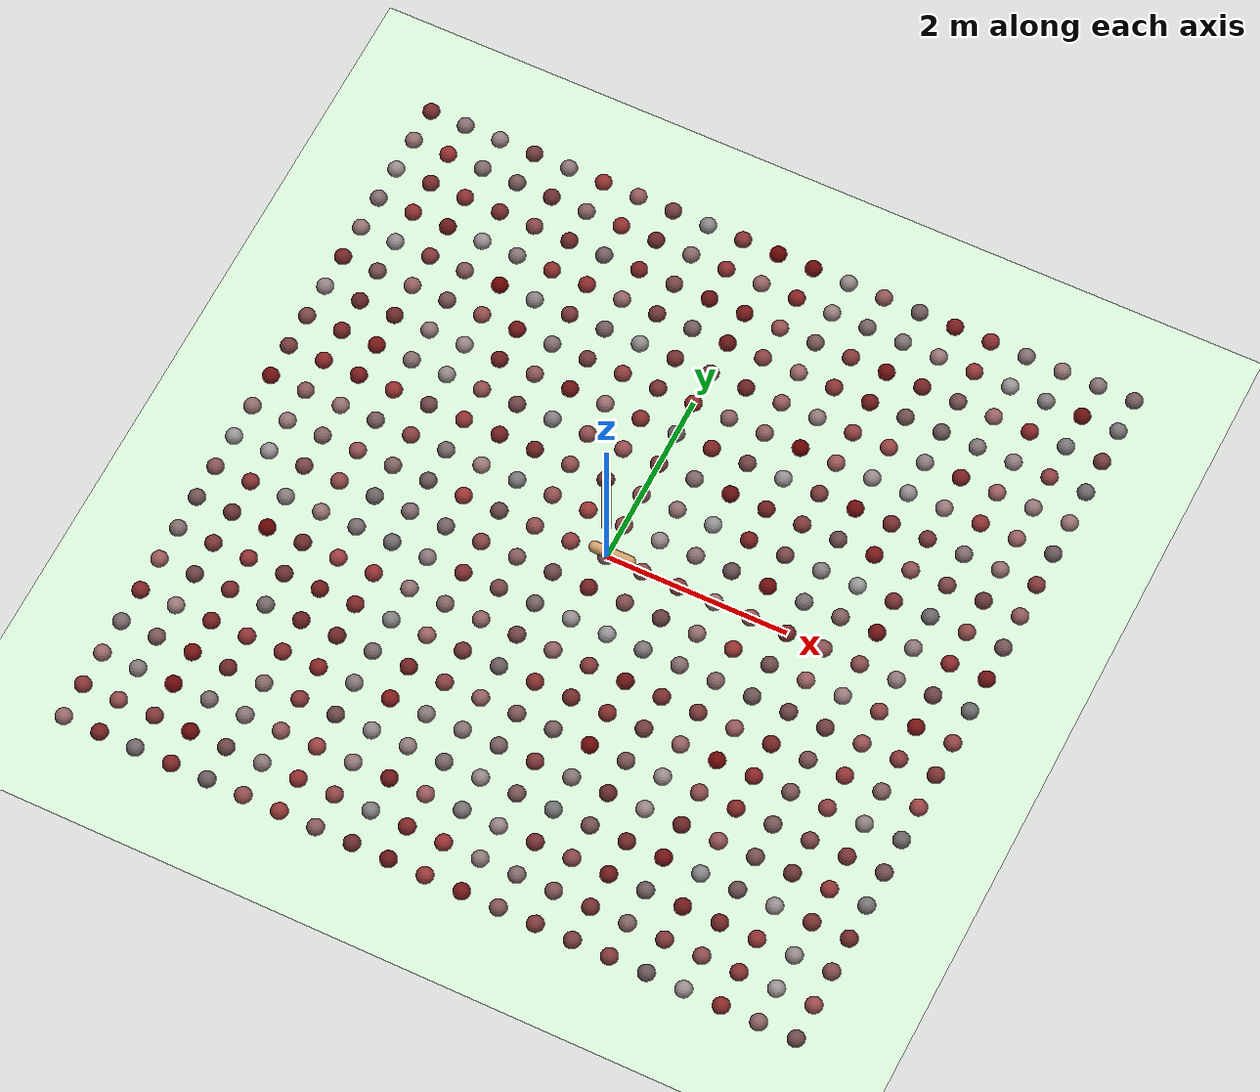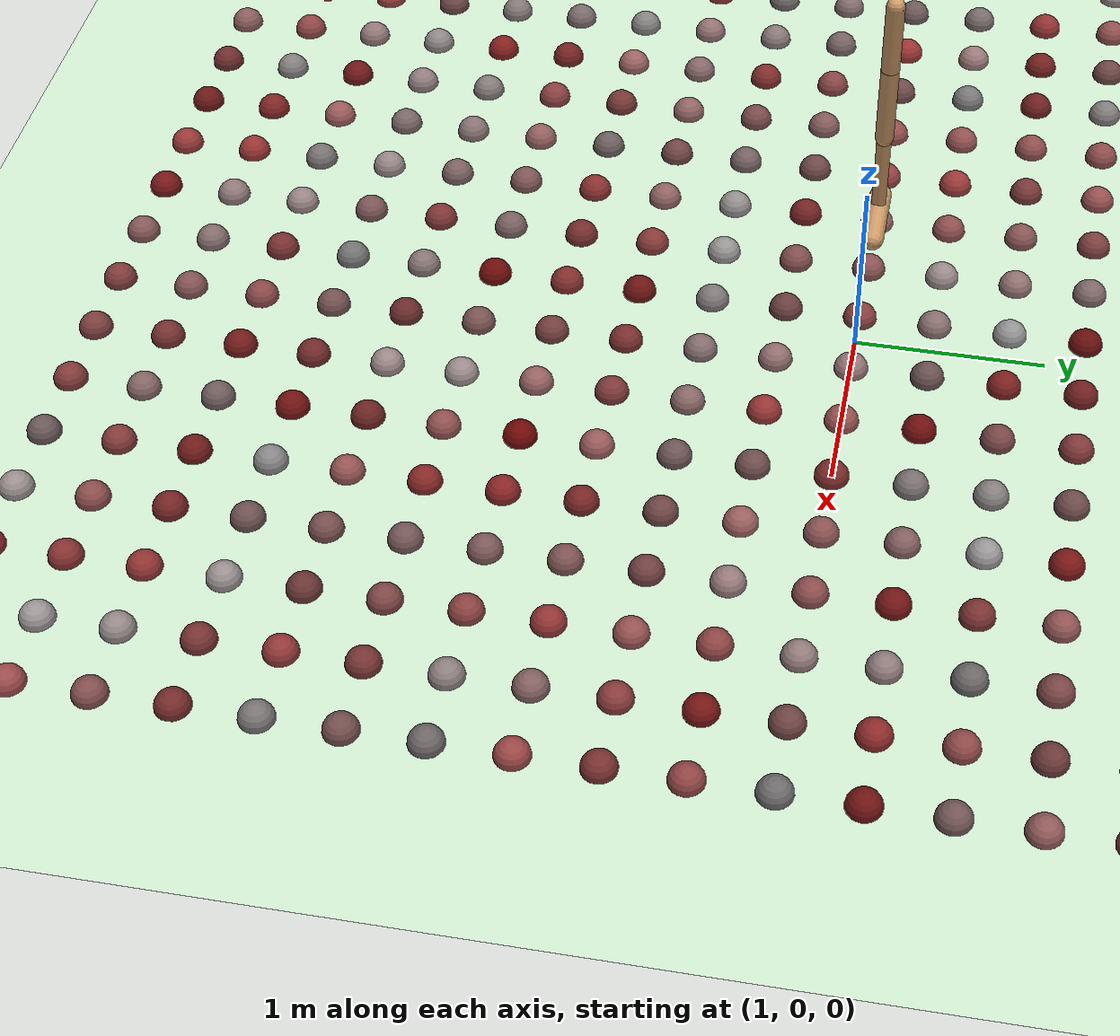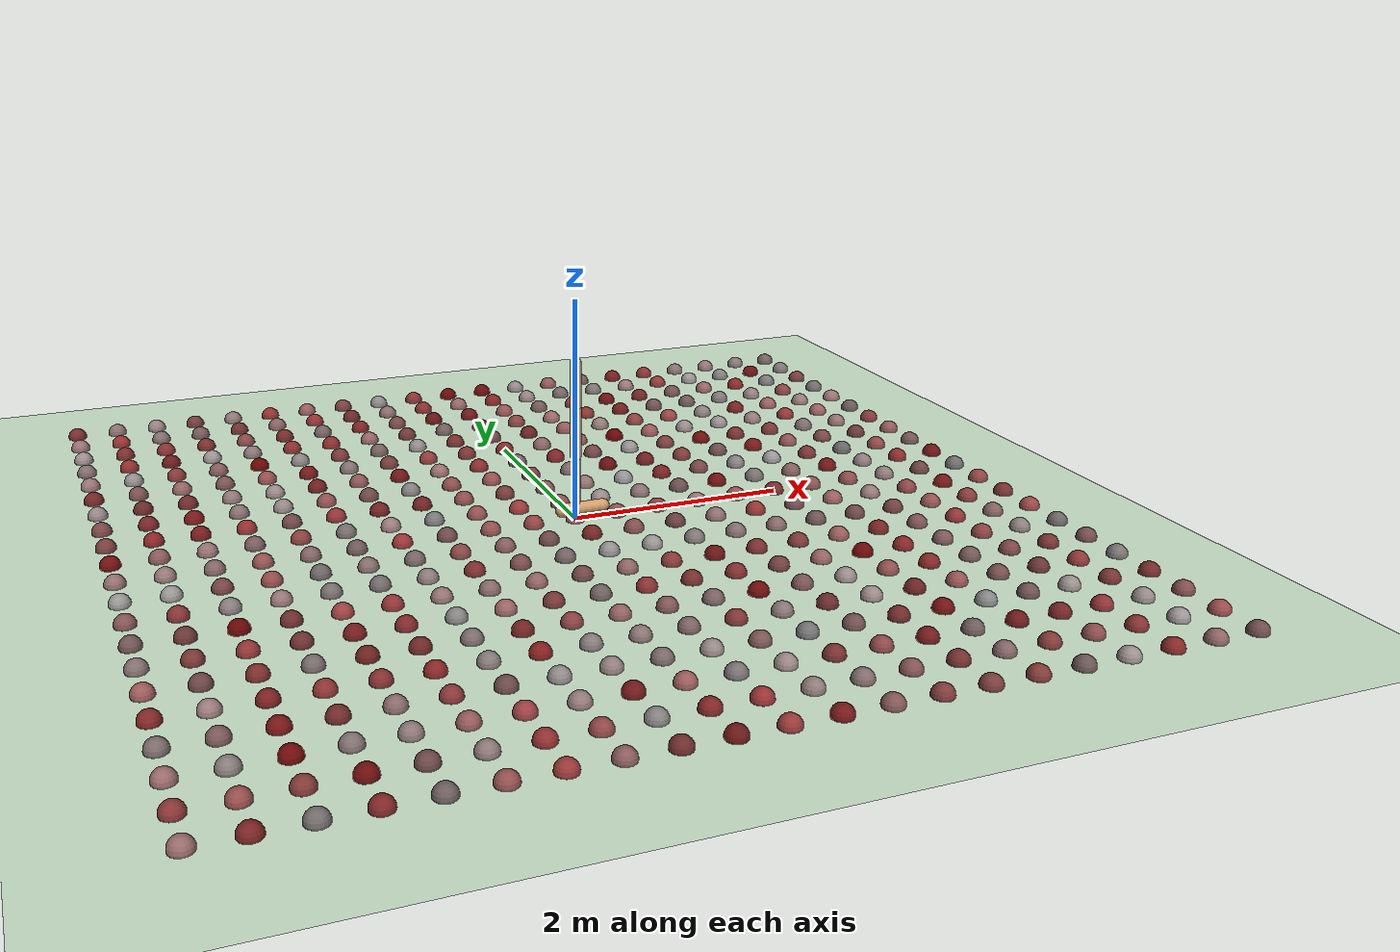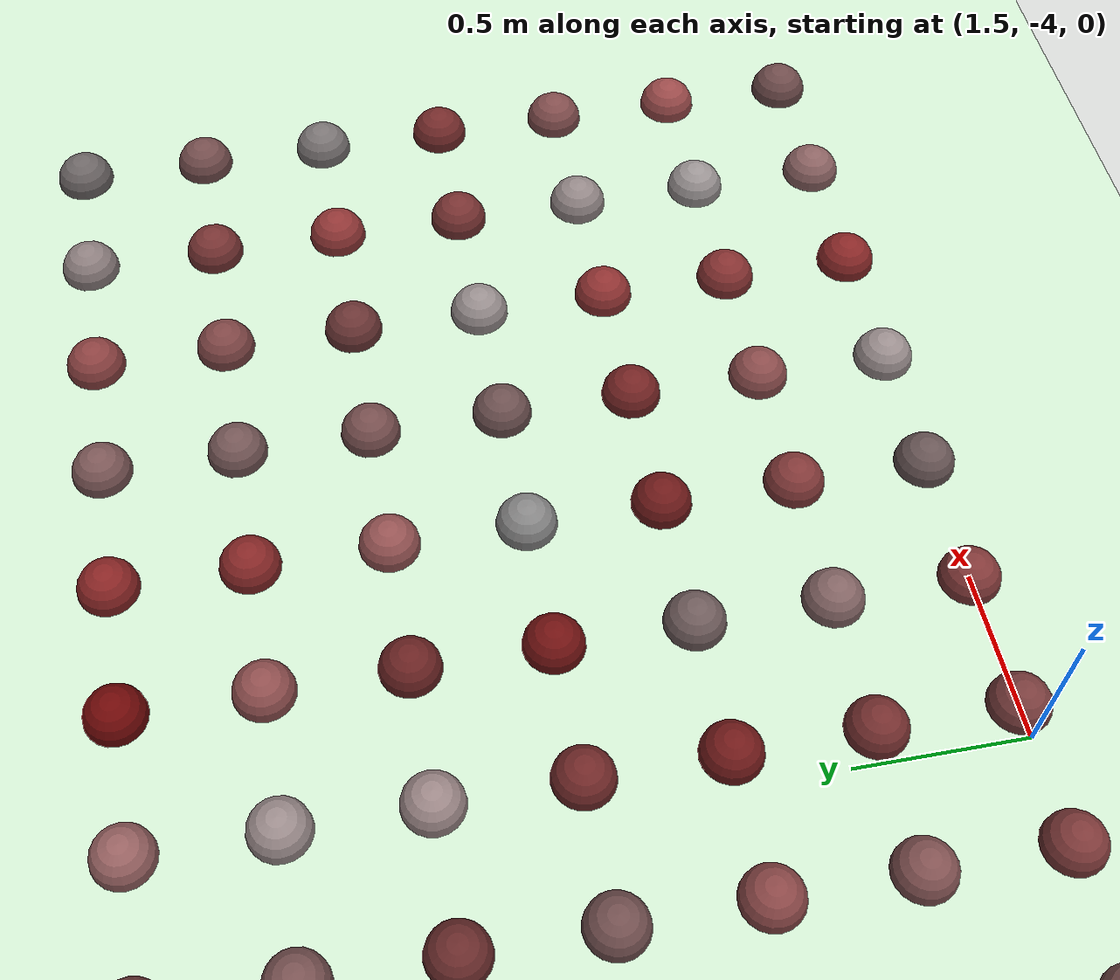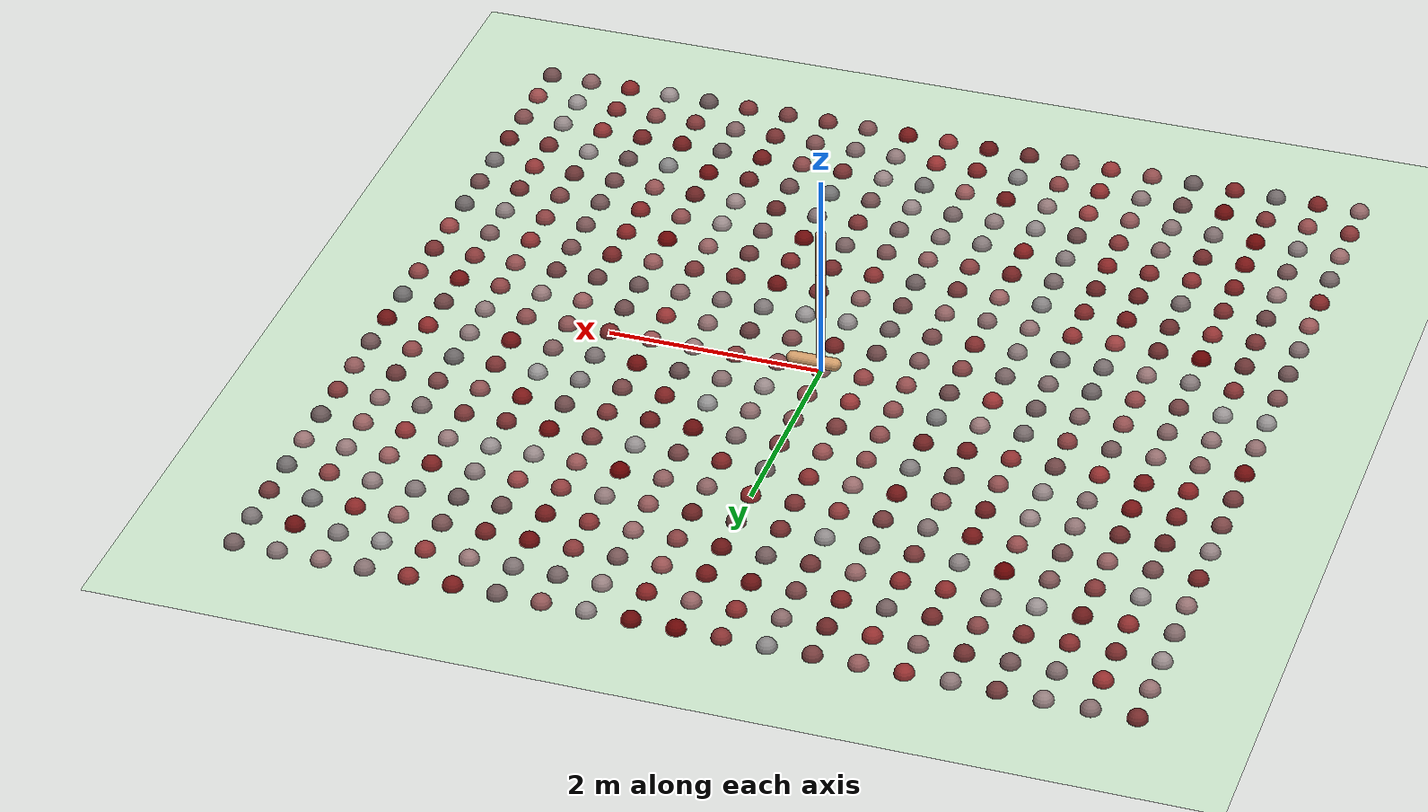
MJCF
<mujoco model="hopper">
  <compiler angle="degree" inertiafromgeom="true"/>
  <default>
    <joint armature="1" damping="1" limited="true"/>
    <geom conaffinity="1" condim="1" contype="1" margin="0.001" material="geom" rgba="0.8 0.6 .4 1" solimp=".8 .8 .01" solref=".02 1"/>
    <motor ctrllimited="true" ctrlrange="-.4 .4"/>
  </default>
  <option integrator="RK4" timestep="0.002"/>
  <visual>
    <map znear="0.02"/>
  </visual>
  <worldbody>
    <light pos="0 0 .6"/>
    <camera name="closeup" pos="0 -4 2" xyaxes="1 0 0 0 1 2"/>
     <!-- Start  sq size 4, spacing 0.4-->
    <geom name="green_sphere_0_0" pos="0.0 0.0 0.001" size=".09" rgba="0.5814032731656413 0.38988673795014084 0.38988673795014084 1.0"/>
<geom name="green_sphere_0_1" pos="0.0 0.4 0.001" size=".09" rgba="0.5463054673462484 0.2962113187412648 0.2962113187412648 1.0"/>
<geom name="green_sphere_0_-1" pos="0.0 -0.4 0.001" size=".09" rgba="0.4424711032160035 0.1292782506542849 0.1292782506542849 1.0"/>
<geom name="green_sphere_0_2" pos="0.0 0.8 0.001" size=".09" rgba="0.5229838213844845 0.32237045988211804 0.32237045988211804 1.0"/>
<geom name="green_sphere_0_-2" pos="0.0 -0.8 0.001" size=".09" rgba="0.5675969774236258 0.5444646491499661 0.5444646491499661 1.0"/>
<geom name="green_sphere_0_3" pos="0.0 1.2000000000000002 0.001" size=".09" rgba="0.4789336921888846 0.2355897455865129 0.2355897455865129 1.0"/>
<geom name="green_sphere_0_-3" pos="0.0 -1.2000000000000002 0.001" size=".09" rgba="0.554999098818954 0.37737412530809966 0.37737412530809966 1.0"/>
<geom name="green_sphere_0_4" pos="0.0 1.6 0.001" size=".09" rgba="0.4360394178840355 0.37522257682542526 0.37522257682542526 1.0"/>
<geom name="green_sphere_0_-4" pos="0.0 -1.6 0.001" size=".09" rgba="0.5267171759494027 0.18003284673829956 0.18003284673829956 1.0"/>
<geom name="green_sphere_0_5" pos="0.0 2.0 0.001" size=".09" rgba="0.5443428092093854 0.15093269502033713 0.15093269502033713 1.0"/>
<geom name="green_sphere_0_-5" pos="0.0 -2.0 0.001" size=".09" rgba="0.48697739373578264 0.32283981856250693 0.32283981856250693 1.0"/>
<geom name="green_sphere_0_6" pos="0.0 2.4000000000000004 0.001" size=".09" rgba="0.434489684450634 0.2518385385254134 0.2518385385254134 1.0"/>
<geom name="green_sphere_0_-6" pos="0.0 -2.4000000000000004 0.001" size=".09" rgba="0.469728040621074 0.369342407108766 0.369342407108766 1.0"/>
<geom name="green_sphere_0_7" pos="0.0 2.8000000000000003 0.001" size=".09" rgba="0.40244827365831787 0.08046343025030395 0.08046343025030395 1.0"/>
<geom name="green_sphere_0_-7" pos="0.0 -2.8000000000000003 0.001" size=".09" rgba="0.5800681825539429 0.5147858015252973 0.5147858015252973 1.0"/>
<geom name="green_sphere_0_8" pos="0.0 3.2 0.001" size=".09" rgba="0.43708687635056687 0.091432378378274 0.091432378378274 1.0"/>
<geom name="green_sphere_0_-8" pos="0.0 -3.2 0.001" size=".09" rgba="0.4579006951253018 0.4327418376423027 0.4327418376423027 1.0"/>
<geom name="green_sphere_0_9" pos="0.0 3.6 0.001" size=".09" rgba="0.580352406874228 0.3853151465013678 0.3853151465013678 1.0"/>
<geom name="green_sphere_0_-9" pos="0.0 -3.6 0.001" size=".09" rgba="0.5833526439570815 0.1875024233044968 0.1875024233044968 1.0"/>
<geom name="green_sphere_0_10" pos="0.0 4.0 0.001" size=".09" rgba="0.40650547155517475 0.020048202283056205 0.020048202283056205 1.0"/>
<geom name="green_sphere_0_-10" pos="0.0 -4.0 0.001" size=".09" rgba="0.5809689266875019 0.21144803228378456 0.21144803228378456 1.0"/>
<geom name="green_sphere_1_0" pos="0.4 0.0 0.001" size=".09" rgba="0.5362708396891072 0.3116398603771403 0.3116398603771403 1.0"/>
<geom name="green_sphere_-1_0" pos="-0.4 0.0 0.001" size=".09" rgba="0.5660485674112462 0.2508570914448053 0.2508570914448053 1.0"/>
<geom name="green_sphere_1_1" pos="0.4 0.4 0.001" size=".09" rgba="0.5887007347796883 0.5272658914340349 0.5272658914340349 1.0"/>
<geom name="green_sphere_-1_1" pos="-0.4 0.4 0.001" size=".09" rgba="0.5976710570360977 0.21480431424330326 0.21480431424330326 1.0"/>
<geom name="green_sphere_1_-1" pos="0.4 -0.4 0.001" size=".09" rgba="0.4971248113674844 0.29370480363185125 0.29370480363185125 1.0"/>
<geom name="green_sphere_-1_-1" pos="-0.4 -0.4 0.001" size=".09" rgba="0.4186398882466735 0.2715903603695273 0.2715903603695273 1.0"/>
<geom name="green_sphere_1_2" pos="0.4 0.8 0.001" size=".09" rgba="0.5633725107328568 0.4306072080587491 0.4306072080587491 1.0"/>
<geom name="green_sphere_-1_2" pos="-0.4 0.8 0.001" size=".09" rgba="0.45774582000607694 0.2116795540033337 0.2116795540033337 1.0"/>
<geom name="green_sphere_1_-2" pos="0.4 -0.8 0.001" size=".09" rgba="0.5797568110663157 0.5649028525675704 0.5649028525675704 1.0"/>
<geom name="green_sphere_-1_-2" pos="-0.4 -0.8 0.001" size=".09" rgba="0.44406356397490154 0.3699409569930732 0.3699409569930732 1.0"/>
<geom name="green_sphere_1_3" pos="0.4 1.2000000000000002 0.001" size=".09" rgba="0.48949322130007855 0.3991173991002885 0.3991173991002885 1.0"/>
<geom name="green_sphere_-1_3" pos="-0.4 1.2000000000000002 0.001" size=".09" rgba="0.5812683688284868 0.30336271490250427 0.30336271490250427 1.0"/>
<geom name="green_sphere_1_-3" pos="0.4 -1.2000000000000002 0.001" size=".09" rgba="0.51795643492148 0.2140090647547866 0.2140090647547866 1.0"/>
<geom name="green_sphere_-1_-3" pos="-0.4 -1.2000000000000002 0.001" size=".09" rgba="0.43198356956797657 0.26426380930634064 0.26426380930634064 1.0"/>
<geom name="green_sphere_1_4" pos="0.4 1.6 0.001" size=".09" rgba="0.48751568730319444 0.13129499684501006 0.13129499684501006 1.0"/>
<geom name="green_sphere_-1_4" pos="-0.4 1.6 0.001" size=".09" rgba="0.5268244450399344 0.17389481728540285 0.17389481728540285 1.0"/>
<geom name="green_sphere_1_-4" pos="0.4 -1.6 0.001" size=".09" rgba="0.45466548811120516 0.1687440168978428 0.1687440168978428 1.0"/>
<geom name="green_sphere_-1_-4" pos="-0.4 -1.6 0.001" size=".09" rgba="0.41626607724284637 0.35910511088669717 0.35910511088669717 1.0"/>
<geom name="green_sphere_1_5" pos="0.4 2.0 0.001" size=".09" rgba="0.5384347824180793 0.37765078236554395 0.37765078236554395 1.0"/>
<geom name="green_sphere_-1_5" pos="-0.4 2.0 0.001" size=".09" rgba="0.4720615531435948 0.18723913723297086 0.18723913723297086 1.0"/>
<geom name="green_sphere_1_-5" pos="0.4 -2.0 0.001" size=".09" rgba="0.46256050128721804 0.36736660549064565 0.36736660549064565 1.0"/>
<geom name="green_sphere_-1_-5" pos="-0.4 -2.0 0.001" size=".09" rgba="0.5646089744988546 0.36201665032720426 0.36201665032720426 1.0"/>
<geom name="green_sphere_1_6" pos="0.4 2.4000000000000004 0.001" size=".09" rgba="0.4100964124613102 0.1277607239891294 0.1277607239891294 1.0"/>
<geom name="green_sphere_-1_6" pos="-0.4 2.4000000000000004 0.001" size=".09" rgba="0.45789081922287644 0.17295109254811297 0.17295109254811297 1.0"/>
<geom name="green_sphere_1_-6" pos="0.4 -2.4000000000000004 0.001" size=".09" rgba="0.4868085441375988 0.19874319980505456 0.19874319980505456 1.0"/>
<geom name="green_sphere_-1_-6" pos="-0.4 -2.4000000000000004 0.001" size=".09" rgba="0.5211749916021587 0.4385431589100371 0.4385431589100371 1.0"/>
<geom name="green_sphere_1_7" pos="0.4 2.8000000000000003 0.001" size=".09" rgba="0.5251087391014146 0.2504229875462742 0.2504229875462742 1.0"/>
<geom name="green_sphere_-1_7" pos="-0.4 2.8000000000000003 0.001" size=".09" rgba="0.44414558046654296 0.35289654862149145 0.35289654862149145 1.0"/>
<geom name="green_sphere_1_-7" pos="0.4 -2.8000000000000003 0.001" size=".09" rgba="0.46903256782830904 0.32245517651430544 0.32245517651430544 1.0"/>
<geom name="green_sphere_-1_-7" pos="-0.4 -2.8000000000000003 0.001" size=".09" rgba="0.4650067261309095 0.391248147758548 0.391248147758548 1.0"/>
<geom name="green_sphere_1_8" pos="0.4 3.2 0.001" size=".09" rgba="0.5874642306163909 0.3162975436282732 0.3162975436282732 1.0"/>
<geom name="green_sphere_-1_8" pos="-0.4 3.2 0.001" size=".09" rgba="0.4072441984374453 0.0718995366125545 0.0718995366125545 1.0"/>
<geom name="green_sphere_1_-8" pos="0.4 -3.2 0.001" size=".09" rgba="0.5870107808349457 0.5087241672526377 0.5087241672526377 1.0"/>
<geom name="green_sphere_-1_-8" pos="-0.4 -3.2 0.001" size=".09" rgba="0.5958290914480711 0.3466128480282508 0.3466128480282508 1.0"/>
<geom name="green_sphere_1_9" pos="0.4 3.6 0.001" size=".09" rgba="0.5174081625217581 0.13120286428224082 0.13120286428224082 1.0"/>
<geom name="green_sphere_-1_9" pos="-0.4 3.6 0.001" size=".09" rgba="0.5357671602979119 0.17172214668508223 0.17172214668508223 1.0"/>
<geom name="green_sphere_1_-9" pos="0.4 -3.6 0.001" size=".09" rgba="0.5534576455747637 0.46128079022194846 0.46128079022194846 1.0"/>
<geom name="green_sphere_-1_-9" pos="-0.4 -3.6 0.001" size=".09" rgba="0.49157118679548434 0.13700959780726546 0.13700959780726546 1.0"/>
<geom name="green_sphere_1_10" pos="0.4 4.0 0.001" size=".09" rgba="0.40583076479307784 0.03621216202365002 0.03621216202365002 1.0"/>
<geom name="green_sphere_-1_10" pos="-0.4 4.0 0.001" size=".09" rgba="0.5234601645043966 0.19262328762718478 0.19262328762718478 1.0"/>
<geom name="green_sphere_1_-10" pos="0.4 -4.0 0.001" size=".09" rgba="0.4523853543356933 0.08601042750027982 0.08601042750027982 1.0"/>
<geom name="green_sphere_-1_-10" pos="-0.4 -4.0 0.001" size=".09" rgba="0.4078803164341862 0.08589385242775638 0.08589385242775638 1.0"/>
<geom name="green_sphere_2_0" pos="0.8 0.0 0.001" size=".09" rgba="0.5194048134479419 0.24156359511886843 0.24156359511886843 1.0"/>
<geom name="green_sphere_-2_0" pos="-0.8 0.0 0.001" size=".09" rgba="0.5721542917464223 0.2979059341680043 0.2979059341680043 1.0"/>
<geom name="green_sphere_2_1" pos="0.8 0.4 0.001" size=".09" rgba="0.5284778140686542 0.4262261485877274 0.4262261485877274 1.0"/>
<geom name="green_sphere_-2_1" pos="-0.8 0.4 0.001" size=".09" rgba="0.5607602694140467 0.30426812743408194 0.30426812743408194 1.0"/>
<geom name="green_sphere_2_-1" pos="0.8 -0.4 0.001" size=".09" rgba="0.4035883697759548 0.2387021781604301 0.2387021781604301 1.0"/>
<geom name="green_sphere_-2_-1" pos="-0.8 -0.4 0.001" size=".09" rgba="0.5097623320705347 0.3503037084131587 0.3503037084131587 1.0"/>
<geom name="green_sphere_2_2" pos="0.8 0.8 0.001" size=".09" rgba="0.5676573037057896 0.5648326331337872 0.5648326331337872 1.0"/>
<geom name="green_sphere_-2_2" pos="-0.8 0.8 0.001" size=".09" rgba="0.5493670342657564 0.29303147469041513 0.29303147469041513 1.0"/>
<geom name="green_sphere_2_-2" pos="0.8 -0.8 0.001" size=".09" rgba="0.48445317997678766 0.4543778221647646 0.4543778221647646 1.0"/>
<geom name="green_sphere_-2_-2" pos="-0.8 -0.8 0.001" size=".09" rgba="0.46526672228769944 0.28223676140420634 0.28223676140420634 1.0"/>
<geom name="green_sphere_2_3" pos="0.8 1.2000000000000002 0.001" size=".09" rgba="0.40021857547153444 0.054140288922569946 0.054140288922569946 1.0"/>
<geom name="green_sphere_-2_3" pos="-0.8 1.2000000000000002 0.001" size=".09" rgba="0.5458654797808877 0.2869580581562127 0.2869580581562127 1.0"/>
<geom name="green_sphere_2_-3" pos="0.8 -1.2000000000000002 0.001" size=".09" rgba="0.4092131881976928 0.06917555497953443 0.06917555497953443 1.0"/>
<geom name="green_sphere_-2_-3" pos="-0.8 -1.2000000000000002 0.001" size=".09" rgba="0.5604292183109456 0.37956091740647246 0.37956091740647246 1.0"/>
<geom name="green_sphere_2_4" pos="0.8 1.6 0.001" size=".09" rgba="0.4430313444637983 0.2563831838065162 0.2563831838065162 1.0"/>
<geom name="green_sphere_-2_4" pos="-0.8 1.6 0.001" size=".09" rgba="0.5959068649962881 0.4214727670373859 0.4214727670373859 1.0"/>
<geom name="green_sphere_2_-4" pos="0.8 -1.6 0.001" size=".09" rgba="0.5013918564347135 0.17095397107914106 0.17095397107914106 1.0"/>
<geom name="green_sphere_-2_-4" pos="-0.8 -1.6 0.001" size=".09" rgba="0.45063709337808056 0.20575713231397555 0.20575713231397555 1.0"/>
<geom name="green_sphere_2_5" pos="0.8 2.0 0.001" size=".09" rgba="0.5509585946975378 0.36314832822709253 0.36314832822709253 1.0"/>
<geom name="green_sphere_-2_5" pos="-0.8 2.0 0.001" size=".09" rgba="0.5481639059035808 0.22230840657742323 0.22230840657742323 1.0"/>
<geom name="green_sphere_2_-5" pos="0.8 -2.0 0.001" size=".09" rgba="0.42122241875395816 0.04115709012649271 0.04115709012649271 1.0"/>
<geom name="green_sphere_-2_-5" pos="-0.8 -2.0 0.001" size=".09" rgba="0.5279705434026888 0.24302564031362944 0.24302564031362944 1.0"/>
<geom name="green_sphere_2_6" pos="0.8 2.4000000000000004 0.001" size=".09" rgba="0.5696107294102968 0.3398342484328304 0.3398342484328304 1.0"/>
<geom name="green_sphere_-2_6" pos="-0.8 2.4000000000000004 0.001" size=".09" rgba="0.5526379913395584 0.5328387954329331 0.5328387954329331 1.0"/>
<geom name="green_sphere_2_-6" pos="0.8 -2.4000000000000004 0.001" size=".09" rgba="0.5144060741492864 0.44407401290339854 0.44407401290339854 1.0"/>
<geom name="green_sphere_-2_-6" pos="-0.8 -2.4000000000000004 0.001" size=".09" rgba="0.5089567199178984 0.46447540071016047 0.46447540071016047 1.0"/>
<geom name="green_sphere_2_7" pos="0.8 2.8000000000000003 0.001" size=".09" rgba="0.5923426580132173 0.4012033549590046 0.4012033549590046 1.0"/>
<geom name="green_sphere_-2_7" pos="-0.8 2.8000000000000003 0.001" size=".09" rgba="0.4360759000716577 0.20212091118488815 0.20212091118488815 1.0"/>
<geom name="green_sphere_2_-7" pos="0.8 -2.8000000000000003 0.001" size=".09" rgba="0.4393998966573794 0.4386234308573273 0.4386234308573273 1.0"/>
<geom name="green_sphere_-2_-7" pos="-0.8 -2.8000000000000003 0.001" size=".09" rgba="0.5564780008000397 0.4794084576256624 0.4794084576256624 1.0"/>
<geom name="green_sphere_2_8" pos="0.8 3.2 0.001" size=".09" rgba="0.458566663634369 0.3312410840296276 0.3312410840296276 1.0"/>
<geom name="green_sphere_-2_8" pos="-0.8 3.2 0.001" size=".09" rgba="0.4621090023509292 0.26199504740117663 0.26199504740117663 1.0"/>
<geom name="green_sphere_2_-8" pos="0.8 -3.2 0.001" size=".09" rgba="0.45875273785259807 0.18243472213805367 0.18243472213805367 1.0"/>
<geom name="green_sphere_-2_-8" pos="-0.8 -3.2 0.001" size=".09" rgba="0.4261985335477224 0.08804837229214935 0.08804837229214935 1.0"/>
<geom name="green_sphere_2_9" pos="0.8 3.6 0.001" size=".09" rgba="0.5831434149043213 0.49330008012101906 0.49330008012101906 1.0"/>
<geom name="green_sphere_-2_9" pos="-0.8 3.6 0.001" size=".09" rgba="0.530371224385548 0.40537040968273097 0.40537040968273097 1.0"/>
<geom name="green_sphere_2_-9" pos="0.8 -3.6 0.001" size=".09" rgba="0.5054854903694 0.4086236223118579 0.4086236223118579 1.0"/>
<geom name="green_sphere_-2_-9" pos="-0.8 -3.6 0.001" size=".09" rgba="0.5017427543881211 0.48692475116677086 0.48692475116677086 1.0"/>
<geom name="green_sphere_2_10" pos="0.8 4.0 0.001" size=".09" rgba="0.5669519676255315 0.5228260680288204 0.5228260680288204 1.0"/>
<geom name="green_sphere_-2_10" pos="-0.8 4.0 0.001" size=".09" rgba="0.5308198409409381 0.5205053481744982 0.5205053481744982 1.0"/>
<geom name="green_sphere_2_-10" pos="0.8 -4.0 0.001" size=".09" rgba="0.508729353847948 0.33042984663436803 0.33042984663436803 1.0"/>
<geom name="green_sphere_-2_-10" pos="-0.8 -4.0 0.001" size=".09" rgba="0.4182011841193815 0.1661925736892944 0.1661925736892944 1.0"/>
<geom name="green_sphere_3_0" pos="1.2000000000000002 0.0 0.001" size=".09" rgba="0.5846722633922565 0.4545928185841192 0.4545928185841192 1.0"/>
<geom name="green_sphere_-3_0" pos="-1.2000000000000002 0.0 0.001" size=".09" rgba="0.4211931752566603 0.2784049883677393 0.2784049883677393 1.0"/>
<geom name="green_sphere_3_1" pos="1.2000000000000002 0.4 0.001" size=".09" rgba="0.4017141258280764 0.3021868271115893 0.3021868271115893 1.0"/>
<geom name="green_sphere_-3_1" pos="-1.2000000000000002 0.4 0.001" size=".09" rgba="0.46500210528268265 0.45962563257606015 0.45962563257606015 1.0"/>
<geom name="green_sphere_3_-1" pos="1.2000000000000002 -0.4 0.001" size=".09" rgba="0.5571431136736087 0.4187186878259169 0.4187186878259169 1.0"/>
<geom name="green_sphere_-3_-1" pos="-1.2000000000000002 -0.4 0.001" size=".09" rgba="0.5226587775289713 0.26138543275860304 0.26138543275860304 1.0"/>
<geom name="green_sphere_3_2" pos="1.2000000000000002 0.8 0.001" size=".09" rgba="0.47687237015123135 0.12094092283307567 0.12094092283307567 1.0"/>
<geom name="green_sphere_-3_2" pos="-1.2000000000000002 0.8 0.001" size=".09" rgba="0.42994941609219534 0.12263404310790615 0.12263404310790615 1.0"/>
<geom name="green_sphere_3_-2" pos="1.2000000000000002 -0.8 0.001" size=".09" rgba="0.5040771756140853 0.4144404497104268 0.4144404497104268 1.0"/>
<geom name="green_sphere_-3_-2" pos="-1.2000000000000002 -0.8 0.001" size=".09" rgba="0.49097742509671033 0.16675679798330467 0.16675679798330467 1.0"/>
<geom name="green_sphere_3_3" pos="1.2000000000000002 1.2000000000000002 0.001" size=".09" rgba="0.4285267842152154 0.11680666033990322 0.11680666033990322 1.0"/>
<geom name="green_sphere_-3_3" pos="-1.2000000000000002 1.2000000000000002 0.001" size=".09" rgba="0.49951206120928937 0.4796320757758846 0.4796320757758846 1.0"/>
<geom name="green_sphere_3_-3" pos="1.2000000000000002 -1.2000000000000002 0.001" size=".09" rgba="0.46612930841225525 0.17417667512646562 0.17417667512646562 1.0"/>
<geom name="green_sphere_-3_-3" pos="-1.2000000000000002 -1.2000000000000002 0.001" size=".09" rgba="0.5165728866341063 0.3942986393871231 0.3942986393871231 1.0"/>
<geom name="green_sphere_3_4" pos="1.2000000000000002 1.6 0.001" size=".09" rgba="0.574100196584072 0.5546159747769339 0.5546159747769339 1.0"/>
<geom name="green_sphere_-3_4" pos="-1.2000000000000002 1.6 0.001" size=".09" rgba="0.42633601326185844 0.08036886275659805 0.08036886275659805 1.0"/>
<geom name="green_sphere_3_-4" pos="1.2000000000000002 -1.6 0.001" size=".09" rgba="0.44024933849016956 0.2340126658589826 0.2340126658589826 1.0"/>
<geom name="green_sphere_-3_-4" pos="-1.2000000000000002 -1.6 0.001" size=".09" rgba="0.5974684964401114 0.3759474675488118 0.3759474675488118 1.0"/>
<geom name="green_sphere_3_5" pos="1.2000000000000002 2.0 0.001" size=".09" rgba="0.4060966995470289 0.009987901985192282 0.009987901985192282 1.0"/>
<geom name="green_sphere_-3_5" pos="-1.2000000000000002 2.0 0.001" size=".09" rgba="0.45002240872902993 0.2239072634821894 0.2239072634821894 1.0"/>
<geom name="green_sphere_3_-5" pos="1.2000000000000002 -2.0 0.001" size=".09" rgba="0.4642557939321743 0.3153231799576479 0.3153231799576479 1.0"/>
<geom name="green_sphere_-3_-5" pos="-1.2000000000000002 -2.0 0.001" size=".09" rgba="0.4425310012032988 0.12846501641403174 0.12846501641403174 1.0"/>
<geom name="green_sphere_3_6" pos="1.2000000000000002 2.4000000000000004 0.001" size=".09" rgba="0.559502335288372 0.46282481307288004 0.46282481307288004 1.0"/>
<geom name="green_sphere_-3_6" pos="-1.2000000000000002 2.4000000000000004 0.001" size=".09" rgba="0.44972553275921867 0.35446522213245185 0.35446522213245185 1.0"/>
<geom name="green_sphere_3_-6" pos="1.2000000000000002 -2.4000000000000004 0.001" size=".09" rgba="0.40236429663135437 0.16344100481779048 0.16344100481779048 1.0"/>
<geom name="green_sphere_-3_-6" pos="-1.2000000000000002 -2.4000000000000004 0.001" size=".09" rgba="0.5141570083888222 0.11429843589308725 0.11429843589308725 1.0"/>
<geom name="green_sphere_3_7" pos="1.2000000000000002 2.8000000000000003 0.001" size=".09" rgba="0.5324235666841751 0.19683855149417395 0.19683855149417395 1.0"/>
<geom name="green_sphere_-3_7" pos="-1.2000000000000002 2.8000000000000003 0.001" size=".09" rgba="0.5713844600207768 0.38162998013540894 0.38162998013540894 1.0"/>
<geom name="green_sphere_3_-7" pos="1.2000000000000002 -2.8000000000000003 0.001" size=".09" rgba="0.4373183890693944 0.3034901945912847 0.3034901945912847 1.0"/>
<geom name="green_sphere_-3_-7" pos="-1.2000000000000002 -2.8000000000000003 0.001" size=".09" rgba="0.5515677893674229 0.5183025973733478 0.5183025973733478 1.0"/>
<geom name="green_sphere_3_8" pos="1.2000000000000002 3.2 0.001" size=".09" rgba="0.5283061628645154 0.2174357505846778 0.2174357505846778 1.0"/>
<geom name="green_sphere_-3_8" pos="-1.2000000000000002 3.2 0.001" size=".09" rgba="0.4825688314417944 0.13249457376670076 0.13249457376670076 1.0"/>
<geom name="green_sphere_3_-8" pos="1.2000000000000002 -3.2 0.001" size=".09" rgba="0.5327795229617651 0.271718556725895 0.271718556725895 1.0"/>
<geom name="green_sphere_-3_-8" pos="-1.2000000000000002 -3.2 0.001" size=".09" rgba="0.5660980821181036 0.46006899186716177 0.46006899186716177 1.0"/>
<geom name="green_sphere_3_9" pos="1.2000000000000002 3.6 0.001" size=".09" rgba="0.44765890874242736 0.381856083002672 0.381856083002672 1.0"/>
<geom name="green_sphere_-3_9" pos="-1.2000000000000002 3.6 0.001" size=".09" rgba="0.41797938906423243 0.1487197025586171 0.1487197025586171 1.0"/>
<geom name="green_sphere_3_-9" pos="1.2000000000000002 -3.6 0.001" size=".09" rgba="0.5006268953543486 0.3157298163127936 0.3157298163127936 1.0"/>
<geom name="green_sphere_-3_-9" pos="-1.2000000000000002 -3.6 0.001" size=".09" rgba="0.5487112884110178 0.26227247949316695 0.26227247949316695 1.0"/>
<geom name="green_sphere_3_10" pos="1.2000000000000002 4.0 0.001" size=".09" rgba="0.5626935270486761 0.3313119459503028 0.3313119459503028 1.0"/>
<geom name="green_sphere_-3_10" pos="-1.2000000000000002 4.0 0.001" size=".09" rgba="0.45558819168322645 0.23531845854478767 0.23531845854478767 1.0"/>
<geom name="green_sphere_3_-10" pos="1.2000000000000002 -4.0 0.001" size=".09" rgba="0.4852359466574985 0.21920550994473414 0.21920550994473414 1.0"/>
<geom name="green_sphere_-3_-10" pos="-1.2000000000000002 -4.0 0.001" size=".09" rgba="0.5290672686804972 0.3497778851396707 0.3497778851396707 1.0"/>
<geom name="green_sphere_4_0" pos="1.6 0.0 0.001" size=".09" rgba="0.5891125241798856 0.312317233090556 0.312317233090556 1.0"/>
<geom name="green_sphere_-4_0" pos="-1.6 0.0 0.001" size=".09" rgba="0.5949898953927455 0.1959507863392772 0.1959507863392772 1.0"/>
<geom name="green_sphere_4_1" pos="1.6 0.4 0.001" size=".09" rgba="0.4245777478280392 0.05534401628460062 0.05534401628460062 1.0"/>
<geom name="green_sphere_-4_1" pos="-1.6 0.4 0.001" size=".09" rgba="0.5990068258714674 0.4650160053434257 0.4650160053434257 1.0"/>
<geom name="green_sphere_4_-1" pos="1.6 -0.4 0.001" size=".09" rgba="0.5782626458578142 0.19635622713931428 0.19635622713931428 1.0"/>
<geom name="green_sphere_-4_-1" pos="-1.6 -0.4 0.001" size=".09" rgba="0.45496909659592705 0.37555239896675807 0.37555239896675807 1.0"/>
<geom name="green_sphere_4_2" pos="1.6 0.8 0.001" size=".09" rgba="0.46240846289658305 0.26617635234380604 0.26617635234380604 1.0"/>
<geom name="green_sphere_-4_2" pos="-1.6 0.8 0.001" size=".09" rgba="0.4444382674199709 0.12184268610196836 0.12184268610196836 1.0"/>
<geom name="green_sphere_4_-2" pos="1.6 -0.8 0.001" size=".09" rgba="0.5261374892740289 0.39242717303033336 0.39242717303033336 1.0"/>
<geom name="green_sphere_-4_-2" pos="-1.6 -0.8 0.001" size=".09" rgba="0.5297959236686104 0.46365528901299774 0.46365528901299774 1.0"/>
<geom name="green_sphere_4_3" pos="1.6 1.2000000000000002 0.001" size=".09" rgba="0.4913571040103234 0.21217197439422625 0.21217197439422625 1.0"/>
<geom name="green_sphere_-4_3" pos="-1.6 1.2000000000000002 0.001" size=".09" rgba="0.4281526872364267 0.26813383603385277 0.26813383603385277 1.0"/>
<geom name="green_sphere_4_-3" pos="1.6 -1.2000000000000002 0.001" size=".09" rgba="0.47838033512812067 0.21349677079008655 0.21349677079008655 1.0"/>
<geom name="green_sphere_-4_-3" pos="-1.6 -1.2000000000000002 0.001" size=".09" rgba="0.5664993652596151 0.43450763733368314 0.43450763733368314 1.0"/>
<geom name="green_sphere_4_4" pos="1.6 1.6 0.001" size=".09" rgba="0.4812752675008961 0.22856586320520755 0.22856586320520755 1.0"/>
<geom name="green_sphere_-4_4" pos="-1.6 1.6 0.001" size=".09" rgba="0.5379506929821791 0.32018339615615465 0.32018339615615465 1.0"/>
<geom name="green_sphere_4_-4" pos="1.6 -1.6 0.001" size=".09" rgba="0.580279137541305 0.3723899199645621 0.3723899199645621 1.0"/>
<geom name="green_sphere_-4_-4" pos="-1.6 -1.6 0.001" size=".09" rgba="0.5085281072607062 0.49597343474254124 0.49597343474254124 1.0"/>
<geom name="green_sphere_4_5" pos="1.6 2.0 0.001" size=".09" rgba="0.5946464640387832 0.3326261075776421 0.3326261075776421 1.0"/>
<geom name="green_sphere_-4_5" pos="-1.6 2.0 0.001" size=".09" rgba="0.4966414044576918 0.4240408993447095 0.4240408993447095 1.0"/>
<geom name="green_sphere_4_-5" pos="1.6 -2.0 0.001" size=".09" rgba="0.5948295013973001 0.5346336559217219 0.5346336559217219 1.0"/>
<geom name="green_sphere_-4_-5" pos="-1.6 -2.0 0.001" size=".09" rgba="0.46928065251951323 0.4051270764250223 0.4051270764250223 1.0"/>
<geom name="green_sphere_4_6" pos="1.6 2.4000000000000004 0.001" size=".09" rgba="0.5581126598868721 0.2387045953104262 0.2387045953104262 1.0"/>
<geom name="green_sphere_-4_6" pos="-1.6 2.4000000000000004 0.001" size=".09" rgba="0.46634875560247224 0.21035433533179554 0.21035433533179554 1.0"/>
<geom name="green_sphere_4_-6" pos="1.6 -2.4000000000000004 0.001" size=".09" rgba="0.5992816458895922 0.5181512925360826 0.5181512925360826 1.0"/>
<geom name="green_sphere_-4_-6" pos="-1.6 -2.4000000000000004 0.001" size=".09" rgba="0.5057325708266021 0.45886462293944513 0.45886462293944513 1.0"/>
<geom name="green_sphere_4_7" pos="1.6 2.8000000000000003 0.001" size=".09" rgba="0.435264382987511 0.09952776492996585 0.09952776492996585 1.0"/>
<geom name="green_sphere_-4_7" pos="-1.6 2.8000000000000003 0.001" size=".09" rgba="0.5365556162084588 0.16489617090550746 0.16489617090550746 1.0"/>
<geom name="green_sphere_4_-7" pos="1.6 -2.8000000000000003 0.001" size=".09" rgba="0.4331731118769919 0.15419810569971332 0.15419810569971332 1.0"/>
<geom name="green_sphere_-4_-7" pos="-1.6 -2.8000000000000003 0.001" size=".09" rgba="0.41128020863035547 0.27005975676963956 0.27005975676963956 1.0"/>
<geom name="green_sphere_4_8" pos="1.6 3.2 0.001" size=".09" rgba="0.42716341208731745 0.054512418373898086 0.054512418373898086 1.0"/>
<geom name="green_sphere_-4_8" pos="-1.6 3.2 0.001" size=".09" rgba="0.4443313119111139 0.3630499129301175 0.3630499129301175 1.0"/>
<geom name="green_sphere_4_-8" pos="1.6 -3.2 0.001" size=".09" rgba="0.4348503993053123 0.09700704514019864 0.09700704514019864 1.0"/>
<geom name="green_sphere_-4_-8" pos="-1.6 -3.2 0.001" size=".09" rgba="0.5935446036768814 0.2416855323044399 0.2416855323044399 1.0"/>
<geom name="green_sphere_4_9" pos="1.6 3.6 0.001" size=".09" rgba="0.48489546989439847 0.43681012468517416 0.43681012468517416 1.0"/>
<geom name="green_sphere_-4_9" pos="-1.6 3.6 0.001" size=".09" rgba="0.5673988029043113 0.17971354886405821 0.17971354886405821 1.0"/>
<geom name="green_sphere_4_-9" pos="1.6 -3.6 0.001" size=".09" rgba="0.448233068451871 0.17888318780099133 0.17888318780099133 1.0"/>
<geom name="green_sphere_-4_-9" pos="-1.6 -3.6 0.001" size=".09" rgba="0.5545870929778205 0.17590539078843132 0.17590539078843132 1.0"/>
<geom name="green_sphere_4_10" pos="1.6 4.0 0.001" size=".09" rgba="0.43922171032756 0.35187474209605224 0.35187474209605224 1.0"/>
<geom name="green_sphere_-4_10" pos="-1.6 4.0 0.001" size=".09" rgba="0.5748761381714753 0.34869565107114825 0.34869565107114825 1.0"/>
<geom name="green_sphere_4_-10" pos="1.6 -4.0 0.001" size=".09" rgba="0.4663123460718284 0.23323827119303778 0.23323827119303778 1.0"/>
<geom name="green_sphere_-4_-10" pos="-1.6 -4.0 0.001" size=".09" rgba="0.5797105418510804 0.20920339175686364 0.20920339175686364 1.0"/>
<geom name="green_sphere_5_0" pos="2.0 0.0 0.001" size=".09" rgba="0.47328420750136213 0.1649062740726796 0.1649062740726796 1.0"/>
<geom name="green_sphere_-5_0" pos="-2.0 0.0 0.001" size=".09" rgba="0.42028202421079297 0.33774431140269984 0.33774431140269984 1.0"/>
<geom name="green_sphere_5_1" pos="2.0 0.4 0.001" size=".09" rgba="0.4659600257769062 0.4255019944853462 0.4255019944853462 1.0"/>
<geom name="green_sphere_-5_1" pos="-2.0 0.4 0.001" size=".09" rgba="0.4564150089949276 0.4100224611598007 0.4100224611598007 1.0"/>
<geom name="green_sphere_5_-1" pos="2.0 -0.4 0.001" size=".09" rgba="0.4227517950723842 0.2889064390552968 0.2889064390552968 1.0"/>
<geom name="green_sphere_-5_-1" pos="-2.0 -0.4 0.001" size=".09" rgba="0.5010412604748543 0.415376725867475 0.415376725867475 1.0"/>
<geom name="green_sphere_5_2" pos="2.0 0.8 0.001" size=".09" rgba="0.5092723769066503 0.4847230903983959 0.4847230903983959 1.0"/>
<geom name="green_sphere_-5_2" pos="-2.0 0.8 0.001" size=".09" rgba="0.5590551883620342 0.19236418742817551 0.19236418742817551 1.0"/>
<geom name="green_sphere_5_-2" pos="2.0 -0.8 0.001" size=".09" rgba="0.4167710235984472 0.32116106371288955 0.32116106371288955 1.0"/>
<geom name="green_sphere_-5_-2" pos="-2.0 -0.8 0.001" size=".09" rgba="0.4275369629095723 0.3986058961642976 0.3986058961642976 1.0"/>
<geom name="green_sphere_5_3" pos="2.0 1.2000000000000002 0.001" size=".09" rgba="0.42073890645213097 0.28261317148902626 0.28261317148902626 1.0"/>
<geom name="green_sphere_-5_3" pos="-2.0 1.2000000000000002 0.001" size=".09" rgba="0.558330755446498 0.30264113333016646 0.30264113333016646 1.0"/>
<geom name="green_sphere_5_-3" pos="2.0 -1.2000000000000002 0.001" size=".09" rgba="0.5854762680027852 0.344552883946291 0.344552883946291 1.0"/>
<geom name="green_sphere_-5_-3" pos="-2.0 -1.2000000000000002 0.001" size=".09" rgba="0.5588159431813717 0.19087596588892475 0.19087596588892475 1.0"/>
<geom name="green_sphere_5_4" pos="2.0 1.6 0.001" size=".09" rgba="0.4341380848437146 0.04917801266343841 0.04917801266343841 1.0"/>
<geom name="green_sphere_-5_4" pos="-2.0 1.6 0.001" size=".09" rgba="0.4263095231363058 0.11536343423885081 0.11536343423885081 1.0"/>
<geom name="green_sphere_5_-4" pos="2.0 -1.6 0.001" size=".09" rgba="0.4277156326325385 0.02900211960138377 0.02900211960138377 1.0"/>
<geom name="green_sphere_-5_-4" pos="-2.0 -1.6 0.001" size=".09" rgba="0.48884159714859704 0.1485141417953305 0.1485141417953305 1.0"/>
<geom name="green_sphere_5_5" pos="2.0 2.0 0.001" size=".09" rgba="0.5852818050924473 0.5267049626142966 0.5267049626142966 1.0"/>
<geom name="green_sphere_-5_5" pos="-2.0 2.0 0.001" size=".09" rgba="0.44583622052165467 0.08461480108721925 0.08461480108721925 1.0"/>
<geom name="green_sphere_5_-5" pos="2.0 -2.0 0.001" size=".09" rgba="0.5530898999933995 0.30218832492421815 0.30218832492421815 1.0"/>
<geom name="green_sphere_-5_-5" pos="-2.0 -2.0 0.001" size=".09" rgba="0.4171109084788692 0.1430417651055751 0.1430417651055751 1.0"/>
<geom name="green_sphere_5_6" pos="2.0 2.4000000000000004 0.001" size=".09" rgba="0.5874412528118079 0.2614364263057666 0.2614364263057666 1.0"/>
<geom name="green_sphere_-5_6" pos="-2.0 2.4000000000000004 0.001" size=".09" rgba="0.5301491120932643 0.49810955605165097 0.49810955605165097 1.0"/>
<geom name="green_sphere_5_-6" pos="2.0 -2.4000000000000004 0.001" size=".09" rgba="0.4074262237947309 0.13256036152368716 0.13256036152368716 1.0"/>
<geom name="green_sphere_-5_-6" pos="-2.0 -2.4000000000000004 0.001" size=".09" rgba="0.5207727492108489 0.13933497363185943 0.13933497363185943 1.0"/>
<geom name="green_sphere_5_7" pos="2.0 2.8000000000000003 0.001" size=".09" rgba="0.4269155415479128 0.30188512808652235 0.30188512808652235 1.0"/>
<geom name="green_sphere_-5_7" pos="-2.0 2.8000000000000003 0.001" size=".09" rgba="0.540072764505239 0.16840588868482254 0.16840588868482254 1.0"/>
<geom name="green_sphere_5_-7" pos="2.0 -2.8000000000000003 0.001" size=".09" rgba="0.43476150034577954 0.06610329200701892 0.06610329200701892 1.0"/>
<geom name="green_sphere_-5_-7" pos="-2.0 -2.8000000000000003 0.001" size=".09" rgba="0.5203698511514667 0.20475636651973927 0.20475636651973927 1.0"/>
<geom name="green_sphere_5_8" pos="2.0 3.2 0.001" size=".09" rgba="0.4448683005779351 0.13278258235937407 0.13278258235937407 1.0"/>
<geom name="green_sphere_-5_8" pos="-2.0 3.2 0.001" size=".09" rgba="0.4433991950631013 0.15483797787387765 0.15483797787387765 1.0"/>
<geom name="green_sphere_5_-8" pos="2.0 -3.2 0.001" size=".09" rgba="0.42491592638626074 0.35095425368912236 0.35095425368912236 1.0"/>
<geom name="green_sphere_-5_-8" pos="-2.0 -3.2 0.001" size=".09" rgba="0.5649031436973277 0.33843385186567415 0.33843385186567415 1.0"/>
<geom name="green_sphere_5_9" pos="2.0 3.6 0.001" size=".09" rgba="0.5899192615517755 0.4536912354100088 0.4536912354100088 1.0"/>
<geom name="green_sphere_-5_9" pos="-2.0 3.6 0.001" size=".09" rgba="0.5210300743688003 0.371114080187449 0.371114080187449 1.0"/>
<geom name="green_sphere_5_-9" pos="2.0 -3.6 0.001" size=".09" rgba="0.5051295600355874 0.38516446569262336 0.38516446569262336 1.0"/>
<geom name="green_sphere_-5_-9" pos="-2.0 -3.6 0.001" size=".09" rgba="0.5374157277710849 0.45294965035130186 0.45294965035130186 1.0"/>
<geom name="green_sphere_5_10" pos="2.0 4.0 0.001" size=".09" rgba="0.4638646200922186 0.09997854271306156 0.09997854271306156 1.0"/>
<geom name="green_sphere_-5_10" pos="-2.0 4.0 0.001" size=".09" rgba="0.5721479439069307 0.18057054814671664 0.18057054814671664 1.0"/>
<geom name="green_sphere_5_-10" pos="2.0 -4.0 0.001" size=".09" rgba="0.5003614470858936 0.2177960513852943 0.2177960513852943 1.0"/>
<geom name="green_sphere_-5_-10" pos="-2.0 -4.0 0.001" size=".09" rgba="0.5617320176754713 0.29961783934482805 0.29961783934482805 1.0"/>
<geom name="green_sphere_6_0" pos="2.4000000000000004 0.0 0.001" size=".09" rgba="0.5313389955795339 0.31188462470302275 0.31188462470302275 1.0"/>
<geom name="green_sphere_-6_0" pos="-2.4000000000000004 0.0 0.001" size=".09" rgba="0.500715854149007 0.37267499714116425 0.37267499714116425 1.0"/>
<geom name="green_sphere_6_1" pos="2.4000000000000004 0.4 0.001" size=".09" rgba="0.5031672269480723 0.3617804427179002 0.3617804427179002 1.0"/>
<geom name="green_sphere_-6_1" pos="-2.4000000000000004 0.4 0.001" size=".09" rgba="0.5282816868223295 0.23956476043443203 0.23956476043443203 1.0"/>
<geom name="green_sphere_6_-1" pos="2.4000000000000004 -0.4 0.001" size=".09" rgba="0.5927476285518446 0.3637328254893337 0.3637328254893337 1.0"/>
<geom name="green_sphere_-6_-1" pos="-2.4000000000000004 -0.4 0.001" size=".09" rgba="0.41548532387463455 0.37948384115434386 0.37948384115434386 1.0"/>
<geom name="green_sphere_6_2" pos="2.4000000000000004 0.8 0.001" size=".09" rgba="0.5831425733888064 0.574836575054259 0.574836575054259 1.0"/>
<geom name="green_sphere_-6_2" pos="-2.4000000000000004 0.8 0.001" size=".09" rgba="0.42919971576376875 0.2671346986330283 0.2671346986330283 1.0"/>
<geom name="green_sphere_6_-2" pos="2.4000000000000004 -0.8 0.001" size=".09" rgba="0.42080449292555355 0.2627595613835919 0.2627595613835919 1.0"/>
<geom name="green_sphere_-6_-2" pos="-2.4000000000000004 -0.8 0.001" size=".09" rgba="0.4550368985534305 0.41506737144027345 0.41506737144027345 1.0"/>
<geom name="green_sphere_6_3" pos="2.4000000000000004 1.2000000000000002 0.001" size=".09" rgba="0.4719836709373009 0.08561309377624127 0.08561309377624127 1.0"/>
<geom name="green_sphere_-6_3" pos="-2.4000000000000004 1.2000000000000002 0.001" size=".09" rgba="0.5710037544064233 0.5149652920855248 0.5149652920855248 1.0"/>
<geom name="green_sphere_6_-3" pos="2.4000000000000004 -1.2000000000000002 0.001" size=".09" rgba="0.4564711536082219 0.13830600274917437 0.13830600274917437 1.0"/>
<geom name="green_sphere_-6_-3" pos="-2.4000000000000004 -1.2000000000000002 0.001" size=".09" rgba="0.5982852098058415 0.24149876285211136 0.24149876285211136 1.0"/>
<geom name="green_sphere_6_4" pos="2.4000000000000004 1.6 0.001" size=".09" rgba="0.4646798954389933 0.17405750959709726 0.17405750959709726 1.0"/>
<geom name="green_sphere_-6_4" pos="-2.4000000000000004 1.6 0.001" size=".09" rgba="0.5959962174826434 0.5135361229544373 0.5135361229544373 1.0"/>
<geom name="green_sphere_6_-4" pos="2.4000000000000004 -1.6 0.001" size=".09" rgba="0.5246313296460409 0.13905715540212604 0.13905715540212604 1.0"/>
<geom name="green_sphere_-6_-4" pos="-2.4000000000000004 -1.6 0.001" size=".09" rgba="0.4465318564771949 0.10255591364192118 0.10255591364192118 1.0"/>
<geom name="green_sphere_6_5" pos="2.4000000000000004 2.0 0.001" size=".09" rgba="0.5796349526802734 0.5484756266766027 0.5484756266766027 1.0"/>
<geom name="green_sphere_-6_5" pos="-2.4000000000000004 2.0 0.001" size=".09" rgba="0.5756548775431427 0.2959361465913962 0.2959361465913962 1.0"/>
<geom name="green_sphere_6_-5" pos="2.4000000000000004 -2.0 0.001" size=".09" rgba="0.5151246445539998 0.14692387176310773 0.14692387176310773 1.0"/>
<geom name="green_sphere_-6_-5" pos="-2.4000000000000004 -2.0 0.001" size=".09" rgba="0.4142707853803101 0.12262257416620365 0.12262257416620365 1.0"/>
<geom name="green_sphere_6_6" pos="2.4000000000000004 2.4000000000000004 0.001" size=".09" rgba="0.5391638255029025 0.47738302393829823 0.47738302393829823 1.0"/>
<geom name="green_sphere_-6_6" pos="-2.4000000000000004 2.4000000000000004 0.001" size=".09" rgba="0.4094057416380045 0.012987538316859448 0.012987538316859448 1.0"/>
<geom name="green_sphere_6_-6" pos="2.4000000000000004 -2.4000000000000004 0.001" size=".09" rgba="0.5739542595743192 0.31799018491136466 0.31799018491136466 1.0"/>
<geom name="green_sphere_-6_-6" pos="-2.4000000000000004 -2.4000000000000004 0.001" size=".09" rgba="0.5085823594586072 0.17259377956128996 0.17259377956128996 1.0"/>
<geom name="green_sphere_6_7" pos="2.4000000000000004 2.8000000000000003 0.001" size=".09" rgba="0.40589211695375277 0.3290532319153967 0.3290532319153967 1.0"/>
<geom name="green_sphere_-6_7" pos="-2.4000000000000004 2.8000000000000003 0.001" size=".09" rgba="0.5166255259142012 0.4444178654131864 0.4444178654131864 1.0"/>
<geom name="green_sphere_6_-7" pos="2.4000000000000004 -2.8000000000000003 0.001" size=".09" rgba="0.5154017134112676 0.5127579256308212 0.5127579256308212 1.0"/>
<geom name="green_sphere_-6_-7" pos="-2.4000000000000004 -2.8000000000000003 0.001" size=".09" rgba="0.522449141845235 0.4003875264712268 0.4003875264712268 1.0"/>
<geom name="green_sphere_6_8" pos="2.4000000000000004 3.2 0.001" size=".09" rgba="0.45384096241368393 0.3050584848255065 0.3050584848255065 1.0"/>
<geom name="green_sphere_-6_8" pos="-2.4000000000000004 3.2 0.001" size=".09" rgba="0.5196899381586054 0.26905075584748445 0.26905075584748445 1.0"/>
<geom name="green_sphere_6_-8" pos="2.4000000000000004 -3.2 0.001" size=".09" rgba="0.42468506780901605 0.09731109300617602 0.09731109300617602 1.0"/>
<geom name="green_sphere_-6_-8" pos="-2.4000000000000004 -3.2 0.001" size=".09" rgba="0.5337919089546358 0.4481371460731137 0.4481371460731137 1.0"/>
<geom name="green_sphere_6_9" pos="2.4000000000000004 3.6 0.001" size=".09" rgba="0.5645325223971758 0.20997420657912946 0.20997420657912946 1.0"/>
<geom name="green_sphere_-6_9" pos="-2.4000000000000004 3.6 0.001" size=".09" rgba="0.4255806411645083 0.1771322421652028 0.1771322421652028 1.0"/>
<geom name="green_sphere_6_-9" pos="2.4000000000000004 -3.6 0.001" size=".09" rgba="0.4990662413396527 0.21509742296191847 0.21509742296191847 1.0"/>
<geom name="green_sphere_-6_-9" pos="-2.4000000000000004 -3.6 0.001" size=".09" rgba="0.41016856063000895 0.2672925957889659 0.2672925957889659 1.0"/>
<geom name="green_sphere_6_10" pos="2.4000000000000004 4.0 0.001" size=".09" rgba="0.5382761619128297 0.17815261449198366 0.17815261449198366 1.0"/>
<geom name="green_sphere_-6_10" pos="-2.4000000000000004 4.0 0.001" size=".09" rgba="0.5419815916461046 0.45801561183015915 0.45801561183015915 1.0"/>
<geom name="green_sphere_6_-10" pos="2.4000000000000004 -4.0 0.001" size=".09" rgba="0.4023629201388293 0.3298664935810002 0.3298664935810002 1.0"/>
<geom name="green_sphere_-6_-10" pos="-2.4000000000000004 -4.0 0.001" size=".09" rgba="0.4102673919922051 0.3556653914901043 0.3556653914901043 1.0"/>
<geom name="green_sphere_7_0" pos="2.8000000000000003 0.0 0.001" size=".09" rgba="0.5342203809389077 0.2923155737157438 0.2923155737157438 1.0"/>
<geom name="green_sphere_-7_0" pos="-2.8000000000000003 0.0 0.001" size=".09" rgba="0.5674456417402712 0.3080629633342386 0.3080629633342386 1.0"/>
<geom name="green_sphere_7_1" pos="2.8000000000000003 0.4 0.001" size=".09" rgba="0.4376110658257192 0.07846443333697789 0.07846443333697789 1.0"/>
<geom name="green_sphere_-7_1" pos="-2.8000000000000003 0.4 0.001" size=".09" rgba="0.45732383809240124 0.3468667077247588 0.3468667077247588 1.0"/>
<geom name="green_sphere_7_-1" pos="2.8000000000000003 -0.4 0.001" size=".09" rgba="0.5816629306303059 0.4657804005057953 0.4657804005057953 1.0"/>
<geom name="green_sphere_-7_-1" pos="-2.8000000000000003 -0.4 0.001" size=".09" rgba="0.5678344917170788 0.2770403067125665 0.2770403067125665 1.0"/>
<geom name="green_sphere_7_2" pos="2.8000000000000003 0.8 0.001" size=".09" rgba="0.46996539524258657 0.18884649189707425 0.18884649189707425 1.0"/>
<geom name="green_sphere_-7_2" pos="-2.8000000000000003 0.8 0.001" size=".09" rgba="0.5668534579989501 0.17913389196819296 0.17913389196819296 1.0"/>
<geom name="green_sphere_7_-2" pos="2.8000000000000003 -0.8 0.001" size=".09" rgba="0.43032426727208817 0.24265199763280065 0.24265199763280065 1.0"/>
<geom name="green_sphere_-7_-2" pos="-2.8000000000000003 -0.8 0.001" size=".09" rgba="0.5792459440862454 0.4448802643505496 0.4448802643505496 1.0"/>
<geom name="green_sphere_7_3" pos="2.8000000000000003 1.2000000000000002 0.001" size=".09" rgba="0.5546395711819503 0.31802891551944323 0.31802891551944323 1.0"/>
<geom name="green_sphere_-7_3" pos="-2.8000000000000003 1.2000000000000002 0.001" size=".09" rgba="0.5197628632278197 0.4187521711733262 0.4187521711733262 1.0"/>
<geom name="green_sphere_7_-3" pos="2.8000000000000003 -1.2000000000000002 0.001" size=".09" rgba="0.48060744888030343 0.31499005678982267 0.31499005678982267 1.0"/>
<geom name="green_sphere_-7_-3" pos="-2.8000000000000003 -1.2000000000000002 0.001" size=".09" rgba="0.415559656156929 0.16700334060085614 0.16700334060085614 1.0"/>
<geom name="green_sphere_7_4" pos="2.8000000000000003 1.6 0.001" size=".09" rgba="0.4679598546102633 0.20408610021525553 0.20408610021525553 1.0"/>
<geom name="green_sphere_-7_4" pos="-2.8000000000000003 1.6 0.001" size=".09" rgba="0.5583076742458544 0.44848622295714896 0.44848622295714896 1.0"/>
<geom name="green_sphere_7_-4" pos="2.8000000000000003 -1.6 0.001" size=".09" rgba="0.47417068648578065 0.3322135658160916 0.3322135658160916 1.0"/>
<geom name="green_sphere_-7_-4" pos="-2.8000000000000003 -1.6 0.001" size=".09" rgba="0.41286153093887756 0.17703539424669598 0.17703539424669598 1.0"/>
<geom name="green_sphere_7_5" pos="2.8000000000000003 2.0 0.001" size=".09" rgba="0.5830008477745485 0.4656783113988543 0.4656783113988543 1.0"/>
<geom name="green_sphere_-7_5" pos="-2.8000000000000003 2.0 0.001" size=".09" rgba="0.4623477325321818 0.3127190319973505 0.3127190319973505 1.0"/>
<geom name="green_sphere_7_-5" pos="2.8000000000000003 -2.0 0.001" size=".09" rgba="0.4453384085413767 0.3281591234010832 0.3281591234010832 1.0"/>
<geom name="green_sphere_-7_-5" pos="-2.8000000000000003 -2.0 0.001" size=".09" rgba="0.4546310785294329 0.39760122073882925 0.39760122073882925 1.0"/>
<geom name="green_sphere_7_6" pos="2.8000000000000003 2.4000000000000004 0.001" size=".09" rgba="0.4729299478357179 0.12127417335930613 0.12127417335930613 1.0"/>
<geom name="green_sphere_-7_6" pos="-2.8000000000000003 2.4000000000000004 0.001" size=".09" rgba="0.5075189835538556 0.34083443048102857 0.34083443048102857 1.0"/>
<geom name="green_sphere_7_-6" pos="2.8000000000000003 -2.4000000000000004 0.001" size=".09" rgba="0.4530876352484322 0.297410597492226 0.297410597492226 1.0"/>
<geom name="green_sphere_-7_-6" pos="-2.8000000000000003 -2.4000000000000004 0.001" size=".09" rgba="0.5410318452153542 0.18883893334946067 0.18883893334946067 1.0"/>
<geom name="green_sphere_7_7" pos="2.8000000000000003 2.8000000000000003 0.001" size=".09" rgba="0.4956841116334971 0.4477848939132408 0.4477848939132408 1.0"/>
<geom name="green_sphere_-7_7" pos="-2.8000000000000003 2.8000000000000003 0.001" size=".09" rgba="0.5912693732674119 0.5560377403446503 0.5560377403446503 1.0"/>
<geom name="green_sphere_7_-7" pos="2.8000000000000003 -2.8000000000000003 0.001" size=".09" rgba="0.41639340671723807 0.30663913067471305 0.30663913067471305 1.0"/>
<geom name="green_sphere_-7_-7" pos="-2.8000000000000003 -2.8000000000000003 0.001" size=".09" rgba="0.4306052163273618 0.15663524254339983 0.15663524254339983 1.0"/>
<geom name="green_sphere_7_8" pos="2.8000000000000003 3.2 0.001" size=".09" rgba="0.5901396649257062 0.38218406744566147 0.38218406744566147 1.0"/>
<geom name="green_sphere_-7_8" pos="-2.8000000000000003 3.2 0.001" size=".09" rgba="0.4667109776519971 0.1647896235511186 0.1647896235511186 1.0"/>
<geom name="green_sphere_7_-8" pos="2.8000000000000003 -3.2 0.001" size=".09" rgba="0.4472443828392371 0.13592655391157366 0.13592655391157366 1.0"/>
<geom name="green_sphere_-7_-8" pos="-2.8000000000000003 -3.2 0.001" size=".09" rgba="0.4891665472799144 0.4234284316177981 0.4234284316177981 1.0"/>
<geom name="green_sphere_7_9" pos="2.8000000000000003 3.6 0.001" size=".09" rgba="0.5787892020511347 0.5632644481483856 0.5632644481483856 1.0"/>
<geom name="green_sphere_-7_9" pos="-2.8000000000000003 3.6 0.001" size=".09" rgba="0.4513149559011797 0.33348328229369884 0.33348328229369884 1.0"/>
<geom name="green_sphere_7_-9" pos="2.8000000000000003 -3.6 0.001" size=".09" rgba="0.5338189971606183 0.2896480281352648 0.2896480281352648 1.0"/>
<geom name="green_sphere_-7_-9" pos="-2.8000000000000003 -3.6 0.001" size=".09" rgba="0.4158871580052218 0.044432741671750375 0.044432741671750375 1.0"/>
<geom name="green_sphere_7_10" pos="2.8000000000000003 4.0 0.001" size=".09" rgba="0.5135802117971837 0.42936375665235116 0.42936375665235116 1.0"/>
<geom name="green_sphere_-7_10" pos="-2.8000000000000003 4.0 0.001" size=".09" rgba="0.43775348630493793 0.21941487595708586 0.21941487595708586 1.0"/>
<geom name="green_sphere_7_-10" pos="2.8000000000000003 -4.0 0.001" size=".09" rgba="0.5948910679771426 0.546305278754494 0.546305278754494 1.0"/>
<geom name="green_sphere_-7_-10" pos="-2.8000000000000003 -4.0 0.001" size=".09" rgba="0.4887959083380736 0.1401581383076873 0.1401581383076873 1.0"/>
<geom name="green_sphere_8_0" pos="3.2 0.0 0.001" size=".09" rgba="0.5607222322180241 0.4702047537776326 0.4702047537776326 1.0"/>
<geom name="green_sphere_-8_0" pos="-3.2 0.0 0.001" size=".09" rgba="0.5097208152305555 0.3802516680210665 0.3802516680210665 1.0"/>
<geom name="green_sphere_8_1" pos="3.2 0.4 0.001" size=".09" rgba="0.5524071016703447 0.4664099999454866 0.4664099999454866 1.0"/>
<geom name="green_sphere_-8_1" pos="-3.2 0.4 0.001" size=".09" rgba="0.5757352438292804 0.4263285936663762 0.4263285936663762 1.0"/>
<geom name="green_sphere_8_-1" pos="3.2 -0.4 0.001" size=".09" rgba="0.545288590721067 0.2593172058691643 0.2593172058691643 1.0"/>
<geom name="green_sphere_-8_-1" pos="-3.2 -0.4 0.001" size=".09" rgba="0.4500810416982171 0.2581386072998943 0.2581386072998943 1.0"/>
<geom name="green_sphere_8_2" pos="3.2 0.8 0.001" size=".09" rgba="0.4089597951808509 0.39042400676486594 0.39042400676486594 1.0"/>
<geom name="green_sphere_-8_2" pos="-3.2 0.8 0.001" size=".09" rgba="0.4624090023074505 0.09856595736681861 0.09856595736681861 1.0"/>
<geom name="green_sphere_8_-2" pos="3.2 -0.8 0.001" size=".09" rgba="0.5757953312251926 0.31022147731735616 0.31022147731735616 1.0"/>
<geom name="green_sphere_-8_-2" pos="-3.2 -0.8 0.001" size=".09" rgba="0.5165577643160968 0.47157719790866953 0.47157719790866953 1.0"/>
<geom name="green_sphere_8_3" pos="3.2 1.2000000000000002 0.001" size=".09" rgba="0.46919235393236636 0.2626726407022659 0.2626726407022659 1.0"/>
<geom name="green_sphere_-8_3" pos="-3.2 1.2000000000000002 0.001" size=".09" rgba="0.4657210021818105 0.08556526811605902 0.08556526811605902 1.0"/>
<geom name="green_sphere_8_-3" pos="3.2 -1.2000000000000002 0.001" size=".09" rgba="0.5616265743146497 0.19647460007686224 0.19647460007686224 1.0"/>
<geom name="green_sphere_-8_-3" pos="-3.2 -1.2000000000000002 0.001" size=".09" rgba="0.4015371390234982 0.01442642501994762 0.01442642501994762 1.0"/>
<geom name="green_sphere_8_4" pos="3.2 1.6 0.001" size=".09" rgba="0.4849916500078014 0.4084425834604129 0.4084425834604129 1.0"/>
<geom name="green_sphere_-8_4" pos="-3.2 1.6 0.001" size=".09" rgba="0.41630040847031563 0.15530959136092953 0.15530959136092953 1.0"/>
<geom name="green_sphere_8_-4" pos="3.2 -1.6 0.001" size=".09" rgba="0.5346721815876745 0.24674412325934975 0.24674412325934975 1.0"/>
<geom name="green_sphere_-8_-4" pos="-3.2 -1.6 0.001" size=".09" rgba="0.5619401882106341 0.1946513126342828 0.1946513126342828 1.0"/>
<geom name="green_sphere_8_5" pos="3.2 2.0 0.001" size=".09" rgba="0.55851662549419 0.1977208486787851 0.1977208486787851 1.0"/>
<geom name="green_sphere_-8_5" pos="-3.2 2.0 0.001" size=".09" rgba="0.573746409478733 0.37131999118095166 0.37131999118095166 1.0"/>
<geom name="green_sphere_8_-5" pos="3.2 -2.0 0.001" size=".09" rgba="0.48431361488837765 0.2632421202116114 0.2632421202116114 1.0"/>
<geom name="green_sphere_-8_-5" pos="-3.2 -2.0 0.001" size=".09" rgba="0.47261729411121706 0.16476632752446518 0.16476632752446518 1.0"/>
<geom name="green_sphere_8_6" pos="3.2 2.4000000000000004 0.001" size=".09" rgba="0.5998771033518088 0.3623160114945102 0.3623160114945102 1.0"/>
<geom name="green_sphere_-8_6" pos="-3.2 2.4000000000000004 0.001" size=".09" rgba="0.5028379758634178 0.20746359197671388 0.20746359197671388 1.0"/>
<geom name="green_sphere_8_-6" pos="3.2 -2.4000000000000004 0.001" size=".09" rgba="0.40703130371359453 0.19927529535017402 0.19927529535017402 1.0"/>
<geom name="green_sphere_-8_-6" pos="-3.2 -2.4000000000000004 0.001" size=".09" rgba="0.4712558909089112 0.11630297765277897 0.11630297765277897 1.0"/>
<geom name="green_sphere_8_7" pos="3.2 2.8000000000000003 0.001" size=".09" rgba="0.5640325066041416 0.4853673917158955 0.4853673917158955 1.0"/>
<geom name="green_sphere_-8_7" pos="-3.2 2.8000000000000003 0.001" size=".09" rgba="0.40733249303157293 0.09654825709779497 0.09654825709779497 1.0"/>
<geom name="green_sphere_8_-7" pos="3.2 -2.8000000000000003 0.001" size=".09" rgba="0.5846408385427804 0.5464146803112448 0.5464146803112448 1.0"/>
<geom name="green_sphere_-8_-7" pos="-3.2 -2.8000000000000003 0.001" size=".09" rgba="0.4596805767623516 0.07470416340524438 0.07470416340524438 1.0"/>
<geom name="green_sphere_8_8" pos="3.2 3.2 0.001" size=".09" rgba="0.5300186438336957 0.1486704959275003 0.1486704959275003 1.0"/>
<geom name="green_sphere_-8_8" pos="-3.2 3.2 0.001" size=".09" rgba="0.5251345984535731 0.176852653587113 0.176852653587113 1.0"/>
<geom name="green_sphere_8_-8" pos="3.2 -3.2 0.001" size=".09" rgba="0.5521408018775145 0.19013379280503906 0.19013379280503906 1.0"/>
<geom name="green_sphere_-8_-8" pos="-3.2 -3.2 0.001" size=".09" rgba="0.42371179572490075 0.032055671413562914 0.032055671413562914 1.0"/>
<geom name="green_sphere_8_9" pos="3.2 3.6 0.001" size=".09" rgba="0.5008203659995716 0.47160640941341797 0.47160640941341797 1.0"/>
<geom name="green_sphere_-8_9" pos="-3.2 3.6 0.001" size=".09" rgba="0.49177536184097703 0.41614901171997853 0.41614901171997853 1.0"/>
<geom name="green_sphere_8_-9" pos="3.2 -3.6 0.001" size=".09" rgba="0.5119751808736066 0.18636939104850164 0.18636939104850164 1.0"/>
<geom name="green_sphere_-8_-9" pos="-3.2 -3.6 0.001" size=".09" rgba="0.4953053745368902 0.20822204621537144 0.20822204621537144 1.0"/>
<geom name="green_sphere_8_10" pos="3.2 4.0 0.001" size=".09" rgba="0.577048725811545 0.44346005681393763 0.44346005681393763 1.0"/>
<geom name="green_sphere_-8_10" pos="-3.2 4.0 0.001" size=".09" rgba="0.5751284795343096 0.4881054606987625 0.4881054606987625 1.0"/>
<geom name="green_sphere_8_-10" pos="3.2 -4.0 0.001" size=".09" rgba="0.5267208039581744 0.1490798424844625 0.1490798424844625 1.0"/>
<geom name="green_sphere_-8_-10" pos="-3.2 -4.0 0.001" size=".09" rgba="0.4326916442546233 0.40275427857969237 0.40275427857969237 1.0"/>
<geom name="green_sphere_9_0" pos="3.6 0.0 0.001" size=".09" rgba="0.4211765628235608 0.25412171819457263 0.25412171819457263 1.0"/>
<geom name="green_sphere_-9_0" pos="-3.6 0.0 0.001" size=".09" rgba="0.575006841519914 0.45602396088991815 0.45602396088991815 1.0"/>
<geom name="green_sphere_9_1" pos="3.6 0.4 0.001" size=".09" rgba="0.542653591752492 0.1576323446157808 0.1576323446157808 1.0"/>
<geom name="green_sphere_-9_1" pos="-3.6 0.4 0.001" size=".09" rgba="0.5233419769252722 0.3417624730688663 0.3417624730688663 1.0"/>
<geom name="green_sphere_9_-1" pos="3.6 -0.4 0.001" size=".09" rgba="0.4522653708418805 0.07841009635072405 0.07841009635072405 1.0"/>
<geom name="green_sphere_-9_-1" pos="-3.6 -0.4 0.001" size=".09" rgba="0.5890972810743943 0.5687180443681138 0.5687180443681138 1.0"/>
<geom name="green_sphere_9_2" pos="3.6 0.8 0.001" size=".09" rgba="0.5484221861731498 0.27205561394401434 0.27205561394401434 1.0"/>
<geom name="green_sphere_-9_2" pos="-3.6 0.8 0.001" size=".09" rgba="0.5373572167278914 0.13881499297899158 0.13881499297899158 1.0"/>
<geom name="green_sphere_9_-2" pos="3.6 -0.8 0.001" size=".09" rgba="0.5251971129004361 0.22118561419660188 0.22118561419660188 1.0"/>
<geom name="green_sphere_-9_-2" pos="-3.6 -0.8 0.001" size=".09" rgba="0.5095171337328638 0.19101910728591004 0.19101910728591004 1.0"/>
<geom name="green_sphere_9_3" pos="3.6 1.2000000000000002 0.001" size=".09" rgba="0.40986437339188414 0.21366622944911645 0.21366622944911645 1.0"/>
<geom name="green_sphere_-9_3" pos="-3.6 1.2000000000000002 0.001" size=".09" rgba="0.45814919625338063 0.13822533044412916 0.13822533044412916 1.0"/>
<geom name="green_sphere_9_-3" pos="3.6 -1.2000000000000002 0.001" size=".09" rgba="0.5054028414586015 0.36761925874860735 0.36761925874860735 1.0"/>
<geom name="green_sphere_-9_-3" pos="-3.6 -1.2000000000000002 0.001" size=".09" rgba="0.40765424015914653 0.20036542063624452 0.20036542063624452 1.0"/>
<geom name="green_sphere_9_4" pos="3.6 1.6 0.001" size=".09" rgba="0.5683371441885834 0.4268263068074485 0.4268263068074485 1.0"/>
<geom name="green_sphere_-9_4" pos="-3.6 1.6 0.001" size=".09" rgba="0.4000193041682012 0.1501741320640676 0.1501741320640676 1.0"/>
<geom name="green_sphere_9_-4" pos="3.6 -1.6 0.001" size=".09" rgba="0.5405591074441445 0.48504426099078696 0.48504426099078696 1.0"/>
<geom name="green_sphere_-9_-4" pos="-3.6 -1.6 0.001" size=".09" rgba="0.46748452129957835 0.1995380366326705 0.1995380366326705 1.0"/>
<geom name="green_sphere_9_5" pos="3.6 2.0 0.001" size=".09" rgba="0.5900193295693268 0.3691266717220243 0.3691266717220243 1.0"/>
<geom name="green_sphere_-9_5" pos="-3.6 2.0 0.001" size=".09" rgba="0.4619514396036887 0.3009091883717252 0.3009091883717252 1.0"/>
<geom name="green_sphere_9_-5" pos="3.6 -2.0 0.001" size=".09" rgba="0.4549276682614209 0.1922027483444067 0.1922027483444067 1.0"/>
<geom name="green_sphere_-9_-5" pos="-3.6 -2.0 0.001" size=".09" rgba="0.40420241397022655 0.2538583710544806 0.2538583710544806 1.0"/>
<geom name="green_sphere_9_6" pos="3.6 2.4000000000000004 0.001" size=".09" rgba="0.58063776301274 0.4627712945811737 0.4627712945811737 1.0"/>
<geom name="green_sphere_-9_6" pos="-3.6 2.4000000000000004 0.001" size=".09" rgba="0.5710485815100758 0.5359357708504283 0.5359357708504283 1.0"/>
<geom name="green_sphere_9_-6" pos="3.6 -2.4000000000000004 0.001" size=".09" rgba="0.5564636825328689 0.20525965707630267 0.20525965707630267 1.0"/>
<geom name="green_sphere_-9_-6" pos="-3.6 -2.4000000000000004 0.001" size=".09" rgba="0.5888363242757995 0.4670465065690818 0.4670465065690818 1.0"/>
<geom name="green_sphere_9_7" pos="3.6 2.8000000000000003 0.001" size=".09" rgba="0.5456352946458558 0.2493086752502151 0.2493086752502151 1.0"/>
<geom name="green_sphere_-9_7" pos="-3.6 2.8000000000000003 0.001" size=".09" rgba="0.5498946919694967 0.1744429043149784 0.1744429043149784 1.0"/>
<geom name="green_sphere_9_-7" pos="3.6 -2.8000000000000003 0.001" size=".09" rgba="0.4594973521303047 0.18943647177310463 0.18943647177310463 1.0"/>
<geom name="green_sphere_-9_-7" pos="-3.6 -2.8000000000000003 0.001" size=".09" rgba="0.4647544503422609 0.32730933971432385 0.32730933971432385 1.0"/>
<geom name="green_sphere_9_8" pos="3.6 3.2 0.001" size=".09" rgba="0.46189494329853265 0.45350321667761934 0.45350321667761934 1.0"/>
<geom name="green_sphere_-9_8" pos="-3.6 3.2 0.001" size=".09" rgba="0.4657209547618049 0.16345216807462132 0.16345216807462132 1.0"/>
<geom name="green_sphere_9_-8" pos="3.6 -3.2 0.001" size=".09" rgba="0.5710704582005866 0.5235879239867423 0.5235879239867423 1.0"/>
<geom name="green_sphere_-9_-8" pos="-3.6 -3.2 0.001" size=".09" rgba="0.5156735625667611 0.46492796360526667 0.46492796360526667 1.0"/>
<geom name="green_sphere_9_9" pos="3.6 3.6 0.001" size=".09" rgba="0.405164427914475 0.060021724365968254 0.060021724365968254 1.0"/>
<geom name="green_sphere_-9_9" pos="-3.6 3.6 0.001" size=".09" rgba="0.5788542927503723 0.1822725289517092 0.1822725289517092 1.0"/>
<geom name="green_sphere_9_-9" pos="3.6 -3.6 0.001" size=".09" rgba="0.5952183797372623 0.5681788345004308 0.5681788345004308 1.0"/>
<geom name="green_sphere_-9_-9" pos="-3.6 -3.6 0.001" size=".09" rgba="0.5723722349303754 0.2907344537544688 0.2907344537544688 1.0"/>
<geom name="green_sphere_9_10" pos="3.6 4.0 0.001" size=".09" rgba="0.5162062868382997 0.44697611070909354 0.44697611070909354 1.0"/>
<geom name="green_sphere_-9_10" pos="-3.6 4.0 0.001" size=".09" rgba="0.5213602556687774 0.4216704193898115 0.4216704193898115 1.0"/>
<geom name="green_sphere_9_-10" pos="3.6 -4.0 0.001" size=".09" rgba="0.5389141332936719 0.38014613253779694 0.38014613253779694 1.0"/>
<geom name="green_sphere_-9_-10" pos="-3.6 -4.0 0.001" size=".09" rgba="0.46850569520333146 0.12656596670961434 0.12656596670961434 1.0"/>
<geom name="green_sphere_10_0" pos="4.0 0.0 0.001" size=".09" rgba="0.41833595825668746 0.40850175069715866 0.40850175069715866 1.0"/>
<geom name="green_sphere_-10_0" pos="-4.0 0.0 0.001" size=".09" rgba="0.5593622791780409 0.42088747748747746 0.42088747748747746 1.0"/>
<geom name="green_sphere_10_1" pos="4.0 0.4 0.001" size=".09" rgba="0.4204815509873338 0.07039996225588979 0.07039996225588979 1.0"/>
<geom name="green_sphere_-10_1" pos="-4.0 0.4 0.001" size=".09" rgba="0.43387575400368317 0.05223898135087773 0.05223898135087773 1.0"/>
<geom name="green_sphere_10_-1" pos="4.0 -0.4 0.001" size=".09" rgba="0.5545079357144832 0.2575801971175201 0.2575801971175201 1.0"/>
<geom name="green_sphere_-10_-1" pos="-4.0 -0.4 0.001" size=".09" rgba="0.5779802027439671 0.563340276140904 0.563340276140904 1.0"/>
<geom name="green_sphere_10_2" pos="4.0 0.8 0.001" size=".09" rgba="0.44008657845125543 0.32518978541926247 0.32518978541926247 1.0"/>
<geom name="green_sphere_-10_2" pos="-4.0 0.8 0.001" size=".09" rgba="0.4590945391069115 0.23099026704442993 0.23099026704442993 1.0"/>
<geom name="green_sphere_10_-2" pos="4.0 -0.8 0.001" size=".09" rgba="0.46344313753740546 0.18225498084745057 0.18225498084745057 1.0"/>
<geom name="green_sphere_-10_-2" pos="-4.0 -0.8 0.001" size=".09" rgba="0.5071336471113397 0.3214590931623591 0.3214590931623591 1.0"/>
<geom name="green_sphere_10_3" pos="4.0 1.2000000000000002 0.001" size=".09" rgba="0.5556226469532072 0.34011971386943524 0.34011971386943524 1.0"/>
<geom name="green_sphere_-10_3" pos="-4.0 1.2000000000000002 0.001" size=".09" rgba="0.4741244365796089 0.2662072037606515 0.2662072037606515 1.0"/>
<geom name="green_sphere_10_-3" pos="4.0 -1.2000000000000002 0.001" size=".09" rgba="0.5945632651518984 0.26441269427215636 0.26441269427215636 1.0"/>
<geom name="green_sphere_-10_-3" pos="-4.0 -1.2000000000000002 0.001" size=".09" rgba="0.42764366721294556 0.31763453051696927 0.31763453051696927 1.0"/>
<geom name="green_sphere_10_4" pos="4.0 1.6 0.001" size=".09" rgba="0.5009318372489746 0.2163401630668696 0.2163401630668696 1.0"/>
<geom name="green_sphere_-10_4" pos="-4.0 1.6 0.001" size=".09" rgba="0.5731142190345593 0.5052473705642163 0.5052473705642163 1.0"/>
<geom name="green_sphere_10_-4" pos="4.0 -1.6 0.001" size=".09" rgba="0.41311212441176776 0.38704617642414496 0.38704617642414496 1.0"/>
<geom name="green_sphere_-10_-4" pos="-4.0 -1.6 0.001" size=".09" rgba="0.5012570936024853 0.4235406376680442 0.4235406376680442 1.0"/>
<geom name="green_sphere_10_5" pos="4.0 2.0 0.001" size=".09" rgba="0.4041694856503978 0.3371942076948017 0.3371942076948017 1.0"/>
<geom name="green_sphere_-10_5" pos="-4.0 2.0 0.001" size=".09" rgba="0.4495564817497017 0.13531502068805906 0.13531502068805906 1.0"/>
<geom name="green_sphere_10_-5" pos="4.0 -2.0 0.001" size=".09" rgba="0.44501449235292967 0.2945675620323045 0.2945675620323045 1.0"/>
<geom name="green_sphere_-10_-5" pos="-4.0 -2.0 0.001" size=".09" rgba="0.5985039891509992 0.3391624137570337 0.3391624137570337 1.0"/>
<geom name="green_sphere_10_6" pos="4.0 2.4000000000000004 0.001" size=".09" rgba="0.5974760627146859 0.4431023601014393 0.4431023601014393 1.0"/>
<geom name="green_sphere_-10_6" pos="-4.0 2.4000000000000004 0.001" size=".09" rgba="0.5804943679865809 0.43973918774856846 0.43973918774856846 1.0"/>
<geom name="green_sphere_10_-6" pos="4.0 -2.4000000000000004 0.001" size=".09" rgba="0.46440422553082683 0.44203756533102667 0.44203756533102667 1.0"/>
<geom name="green_sphere_-10_-6" pos="-4.0 -2.4000000000000004 0.001" size=".09" rgba="0.5006946955135956 0.14064081342887452 0.14064081342887452 1.0"/>
<geom name="green_sphere_10_7" pos="4.0 2.8000000000000003 0.001" size=".09" rgba="0.4274216840565857 0.4104782713920658 0.4104782713920658 1.0"/>
<geom name="green_sphere_-10_7" pos="-4.0 2.8000000000000003 0.001" size=".09" rgba="0.5016893420369964 0.4081197354605208 0.4081197354605208 1.0"/>
<geom name="green_sphere_10_-7" pos="4.0 -2.8000000000000003 0.001" size=".09" rgba="0.44586030213625855 0.16058759598542105 0.16058759598542105 1.0"/>
<geom name="green_sphere_-10_-7" pos="-4.0 -2.8000000000000003 0.001" size=".09" rgba="0.46334280956381274 0.40158248964903 0.40158248964903 1.0"/>
<geom name="green_sphere_10_8" pos="4.0 3.2 0.001" size=".09" rgba="0.45285114576144797 0.22582826020280908 0.22582826020280908 1.0"/>
<geom name="green_sphere_-10_8" pos="-4.0 3.2 0.001" size=".09" rgba="0.5899269456287478 0.5366081782849212 0.5366081782849212 1.0"/>
<geom name="green_sphere_10_-8" pos="4.0 -3.2 0.001" size=".09" rgba="0.49907534778369206 0.2954857926369697 0.2954857926369697 1.0"/>
<geom name="green_sphere_-10_-8" pos="-4.0 -3.2 0.001" size=".09" rgba="0.588697027844557 0.4025951479540349 0.4025951479540349 1.0"/>
<geom name="green_sphere_10_9" pos="4.0 3.6 0.001" size=".09" rgba="0.47460057746071854 0.4464341486560754 0.4464341486560754 1.0"/>
<geom name="green_sphere_-10_9" pos="-4.0 3.6 0.001" size=".09" rgba="0.5752362964290785 0.4323465653733524 0.4323465653733524 1.0"/>
<geom name="green_sphere_10_-9" pos="4.0 -3.6 0.001" size=".09" rgba="0.5966228381848699 0.28437297358861024 0.28437297358861024 1.0"/>
<geom name="green_sphere_-10_-9" pos="-4.0 -3.6 0.001" size=".09" rgba="0.5197784126549457 0.19913584856460909 0.19913584856460909 1.0"/>
<geom name="green_sphere_10_10" pos="4.0 4.0 0.001" size=".09" rgba="0.4456693197356894 0.36570891816030776 0.36570891816030776 1.0"/>
<geom name="green_sphere_-10_10" pos="-4.0 4.0 0.001" size=".09" rgba="0.45034463511789363 0.1651414252480392 0.1651414252480392 1.0"/>
<geom name="green_sphere_10_-10" pos="4.0 -4.0 0.001" size=".09" rgba="0.42583897716959895 0.28885215122408553 0.28885215122408553 1.0"/>
<geom name="green_sphere_-10_-10" pos="-4.0 -4.0 0.001" size=".09" rgba="0.5777068123941356 0.40459860931895364 0.40459860931895364 1.0"/>

    <!-- End -->
    <light cutoff="100" diffuse="1 1 1" dir="-0 0 -1.3" directional="true" exponent="1" pos="0 0 1.3" specular=".1 .1 .1"/>
    <geom conaffinity="1" condim="3" name="floor" pos="0 0 0" rgba="0.8 0.9 0.8 1" size="20 20 .125" type="plane" material="MatPlane"/>
    <body name="torso" pos="0 0 1.25">
      <camera name="track" mode="trackcom" pos="0 -3 -0.25" xyaxes="1 0 0 0 0 1"/>
      <joint armature="0" axis="1 0 0" damping="0" limited="false" name="rootx" pos="0 0 -1.25" stiffness="0" type="slide"/>
      <joint armature="0" axis="0 0 1" damping="0" limited="false" name="rootz" pos="0 0 -1.25" ref="1.25" stiffness="0" type="slide"/>
      <joint armature="0" axis="0 1 0" damping="0" limited="false" name="rooty" pos="0 0 0" stiffness="0" type="hinge"/>
      <geom friction="0.9" name="torso_geom" size="0.05 0.19999999999999996" type="capsule"/>
      <body name="thigh" pos="0 0 -0.19999999999999996">
        <joint axis="0 -1 0" name="thigh_joint" pos="0 0 0" range="-150 0" type="hinge"/>
        <geom friction="0.9" pos="0 0 -0.22500000000000009" name="thigh_geom" size="0.05 0.22500000000000003" type="capsule"/>
        <body name="leg" pos="0 0 -0.70000000000000007">
          <joint axis="0 -1 0" name="leg_joint" pos="0 0 0.25" range="-150 0" type="hinge"/>
          <geom friction="0.9" name="leg_geom" size="0.04 0.25" type="capsule"/>
          <body name="foot" pos="0.13 0 -0.35">
            <joint axis="0 -1 0" name="foot_joint" pos="-0.13 0 0.1" range="-45 45" type="hinge"/>
            <geom friction="2.0" pos="-0.065 0 0.1" quat="0.70710678118654757 0 -0.70710678118654746 0" name="foot_geom" size="0.06 0.195" type="capsule"/>
          </body>
        </body>
      </body>
    </body>
  </worldbody>
  <actuator>
    <motor ctrllimited="true" ctrlrange="-1.0 1.0" gear="200.0" joint="thigh_joint"/>
    <motor ctrllimited="true" ctrlrange="-1.0 1.0" gear="200.0" joint="leg_joint"/>
    <motor ctrllimited="true" ctrlrange="-1.0 1.0" gear="200.0" joint="foot_joint"/>
  </actuator>
    <asset>
        <texture type="skybox" builtin="gradient" rgb1=".4 .5 .6" rgb2="0 0 0"
            width="100" height="100"/>
        <texture builtin="flat" height="1278" mark="cross" markrgb="1 1 1" name="texgeom" random="0.01" rgb1="0.8 0.6 0.4" rgb2="0.8 0.6 0.4" type="cube" width="127"/>
        <texture builtin="checker" height="100" name="texplane" rgb1="0 0 0" rgb2="0.8 0.8 0.8" type="2d" width="100"/>
        <material name="MatPlane" reflectance="0.5" shininess="1" specular="1" texrepeat="5 5" texture="texplane"/>
        <material name="geom" texture="texgeom" texuniform="true"/>
    </asset>
</mujoco>
